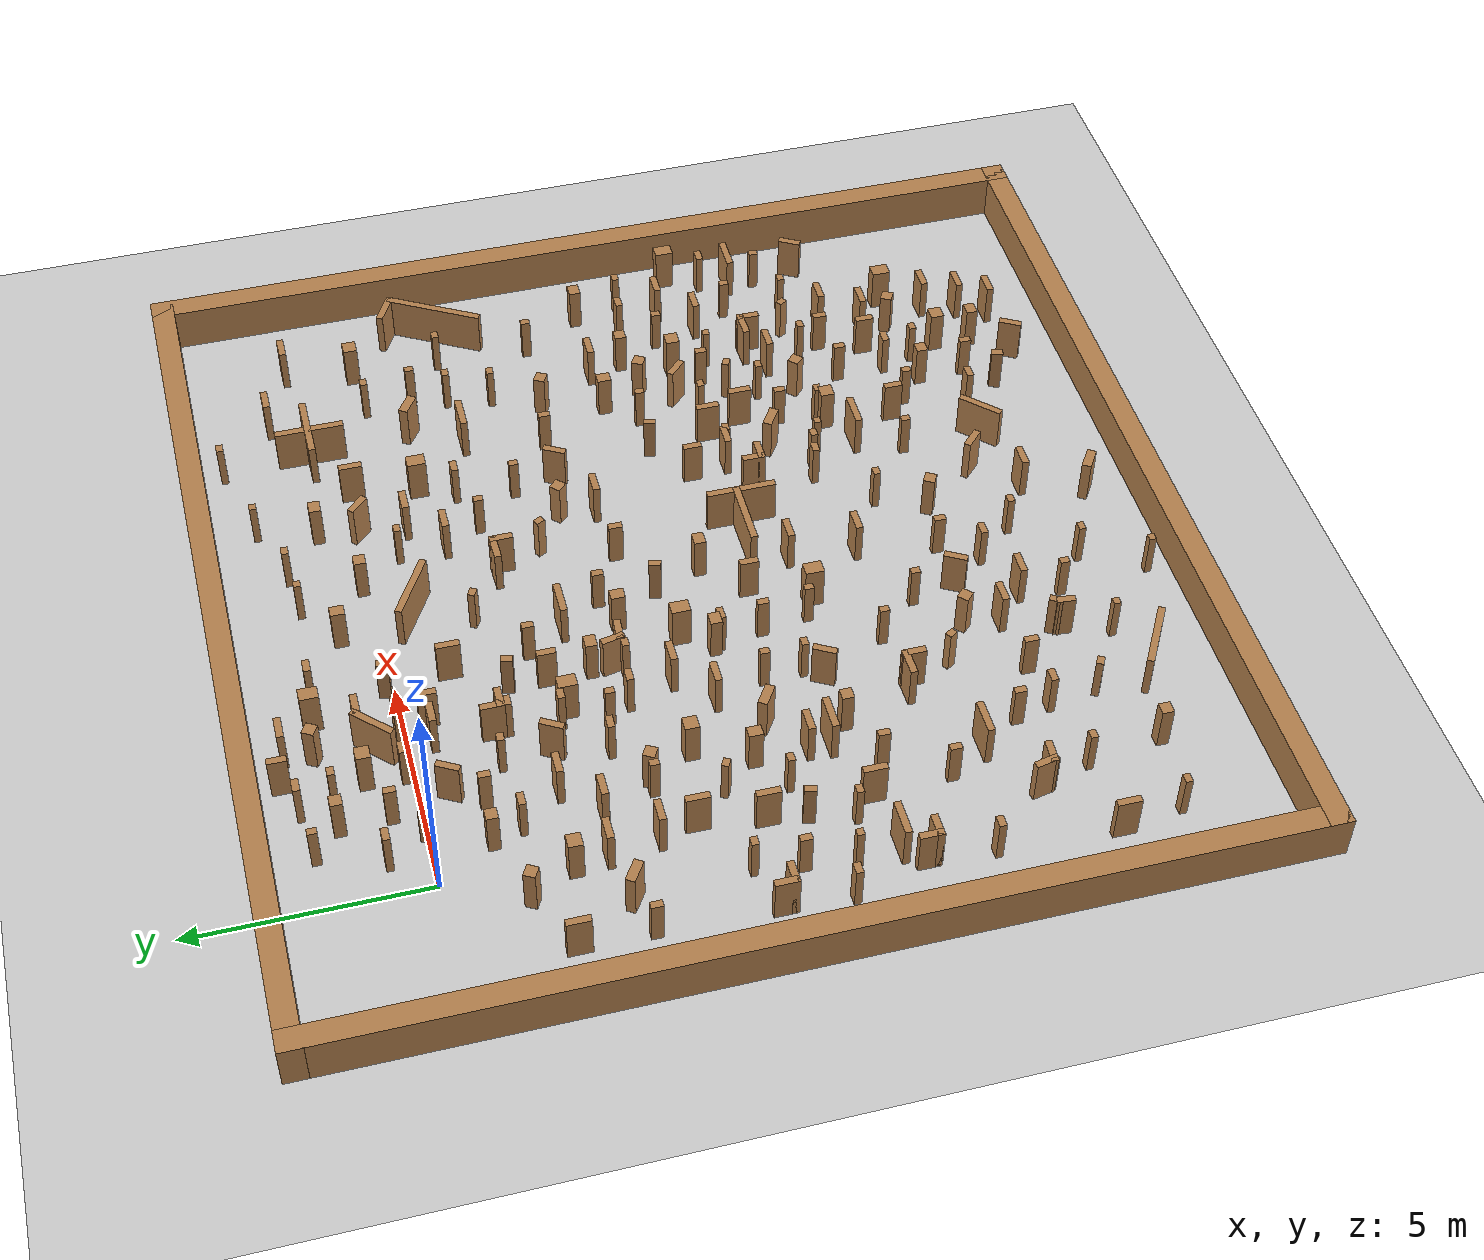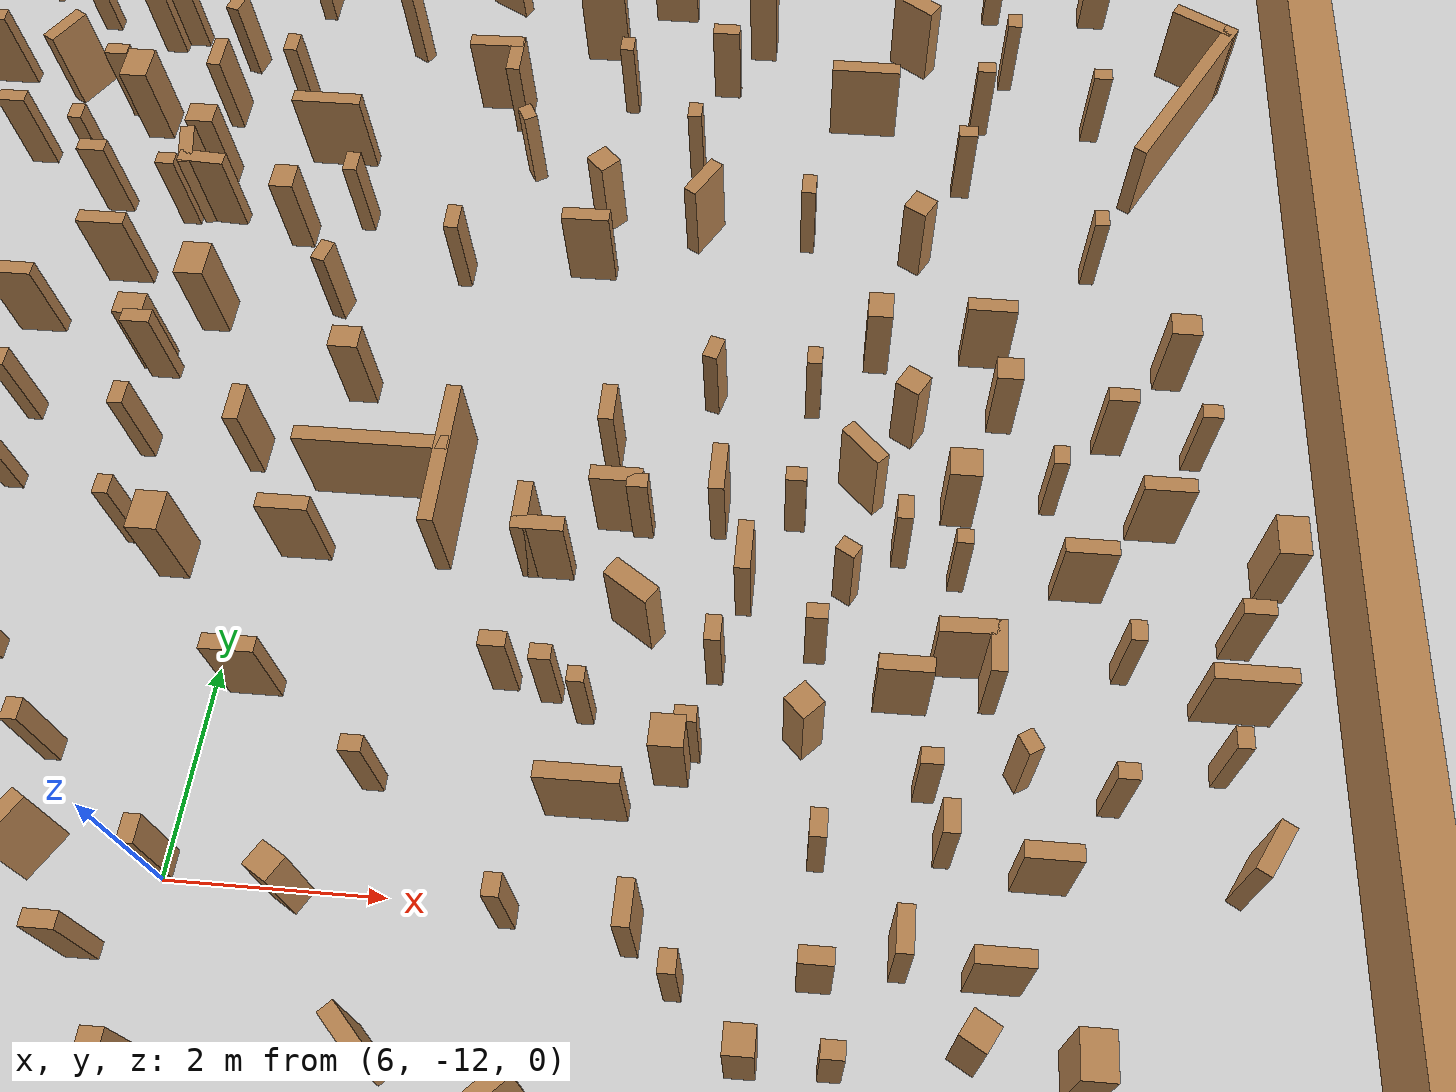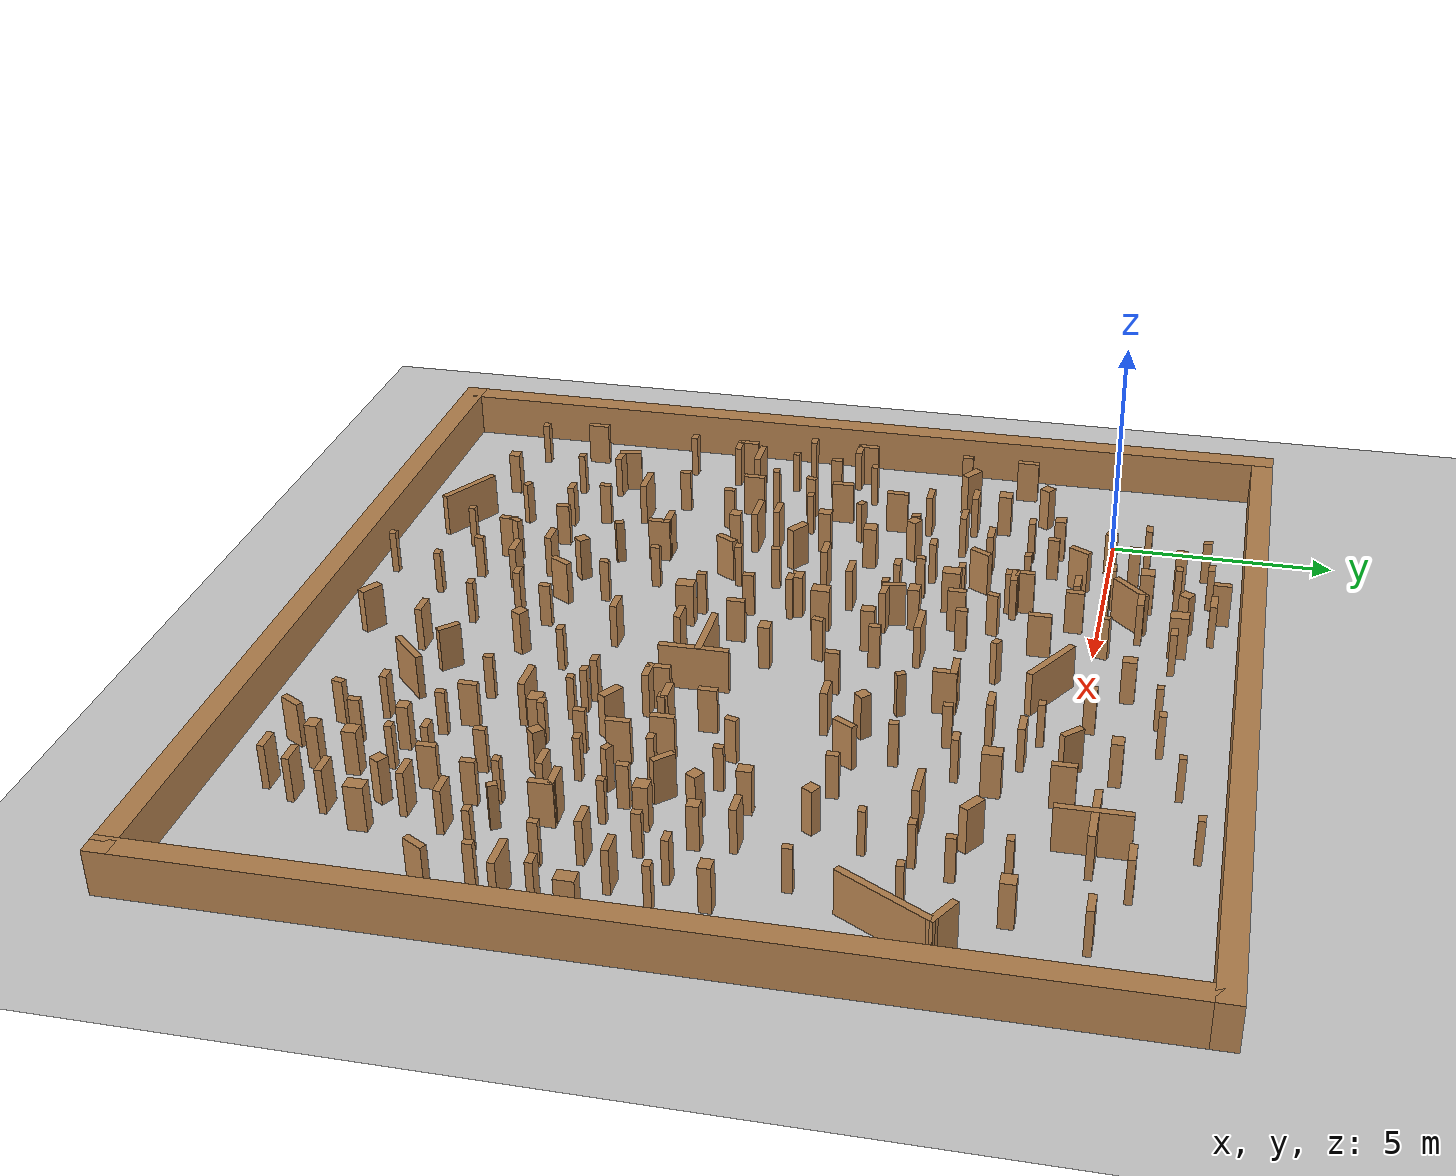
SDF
<sdf version="1.7">
 <world name="default">
  <light name="sun" type="directional">
   <pose>0 0 10 0 -0 0</pose>
   <diffuse>0.8 0.8 0.8 1</diffuse>
   <specular>0.2 0.2 0.2 1</specular>
   <attenuation>
    <range>1000</range>
    <constant>0.9</constant>
    <linear>0.01</linear>
    <quadratic>0.001</quadratic>
   </attenuation>
   <direction>-0.5 0.1 -0.9</direction>
   <spot><inner_angle>0</inner_angle><outer_angle>0</outer_angle><falloff>0</falloff></spot>
  </light>
  <model name="ground_plane">
   <static>1</static>
   <link name="link">
    <collision name="collision">
     <geometry><plane><normal>0 0 1</normal><size>100 100</size></plane></geometry>
     <surface><friction><ode><mu>100</mu><mu2>50</mu2></ode></friction></surface>
    </collision>
    <visual name="visual">
     <cast_shadows>0</cast_shadows>
     <geometry><plane><normal>0 0 1</normal><size>100 100</size></plane></geometry>
     <material>
      <script><uri>file://media/materials/scripts/gazebo.material</uri><name>Gazebo/Grey</name></script>
     </material>
    </visual>
   </link>
  </model>
  <gravity>0 0 -9.8</gravity>
  <magnetic_field>6e-06 2.3e-05 -4.2e-05</magnetic_field>
  <atmosphere type="adiabatic"/>
  <physics type="ode">
   <max_step_size>0.001</max_step_size>
   <real_time_factor>1</real_time_factor>
   <real_time_update_rate>1000</real_time_update_rate>
  </physics>
  <scene><ambient>0.4 0.4 0.4 1</ambient><background>0.7 0.7 0.7 1</background><shadows>1</shadows></scene>
  <spherical_coordinates>
   <surface_model>EARTH_WGS84</surface_model>
   <latitude_deg>0</latitude_deg>
   <longitude_deg>0</longitude_deg>
   <elevation>0</elevation>
   <heading_deg>0</heading_deg>
  </spherical_coordinates>
  <model name="boundary20x20">
   <pose>6.69964 -6.73932 0 0 -0 0</pose>
   <link name="Wall_0">
    <collision name="Wall_0_Collision">
     <geometry><box><size>20.5 0.5 1</size></box></geometry>
     <pose>0 0 0.5 0 -0 0</pose>
    </collision>
    <visual name="Wall_0_Visual">
     <pose>0 0 0.5 0 -0 0</pose>
     <geometry><box><size>20.5 0.5 1</size></box></geometry>
     <material>
      <script><uri>file://media/materials/scripts/gazebo.material</uri><name>Gazebo/Wood</name></script>
      <ambient>1 1 1 1</ambient>
     </material>
     <meta><layer>0</layer></meta>
    </visual>
    <pose>0 -10 0 0 -0 0</pose>
   </link>
   <link name="Wall_2">
    <collision name="Wall_2_Collision">
     <geometry><box><size>20.5 0.5 1</size></box></geometry>
     <pose>0 0 0.5 0 -0 0</pose>
    </collision>
    <visual name="Wall_2_Visual">
     <pose>0 0 0.5 0 -0 0</pose>
     <geometry><box><size>20.5 0.5 1</size></box></geometry>
     <material>
      <script><uri>file://media/materials/scripts/gazebo.material</uri><name>Gazebo/Wood</name></script>
      <ambient>1 1 1 1</ambient>
     </material>
     <meta><layer>0</layer></meta>
    </visual>
    <pose>-10 0 0 0 -0 -1.5708</pose>
   </link>
   <link name="Wall_4">
    <collision name="Wall_4_Collision">
     <geometry><box><size>20.5 0.5 1</size></box></geometry>
     <pose>0 0 0.5 0 -0 0</pose>
    </collision>
    <visual name="Wall_4_Visual">
     <pose>0 0 0.5 0 -0 0</pose>
     <geometry><box><size>20.5 0.5 1</size></box></geometry>
     <material>
      <script><uri>file://media/materials/scripts/gazebo.material</uri><name>Gazebo/Wood</name></script>
      <ambient>1 1 1 1</ambient>
     </material>
     <meta><layer>0</layer></meta>
    </visual>
    <pose>0 10 0 0 -0 0</pose>
   </link>
   <link name="Wall_8">
    <collision name="Wall_8_Collision">
     <geometry><box><size>20.5 0.5 1</size></box></geometry>
     <pose>0 0 0.5 0 -0 0</pose>
    </collision>
    <visual name="Wall_8_Visual">
     <pose>0 0 0.5 0 -0 0</pose>
     <geometry><box><size>20.5 0.5 1</size></box></geometry>
     <material>
      <script><uri>file://media/materials/scripts/gazebo.material</uri><name>Gazebo/Wood</name></script>
      <ambient>1 1 1 1</ambient>
     </material>
     <meta><layer>0</layer></meta>
    </visual>
    <pose>10 0 0 0 -0 1.5708</pose>
   </link>
   <static>1</static>
  </model>
  <model name="t1">
   <pose>4.20156 -11.2326 0 0 -0 0</pose>
   <link name="Wall_0">
    <collision name="Wall_0_Collision">
     <geometry><box><size>0.5 0.15 1</size></box></geometry>
     <pose>0 0 0.5 0 -0 0</pose>
    </collision>
    <visual name="Wall_0_Visual">
     <pose>0 0 0.5 0 -0 0</pose>
     <geometry><box><size>0.5 0.15 1</size></box></geometry>
     <material>
      <script><uri>file://media/materials/scripts/gazebo.material</uri><name>Gazebo/Wood</name></script>
      <ambient>1 1 1 1</ambient>
     </material>
     <meta><layer>0</layer></meta>
    </visual>
    <pose>0.174862 -1.84619 0 0 -0 0</pose>
   </link>
   <link name="Wall_10">
    <collision name="Wall_10_Collision">
     <geometry><box><size>0.16 0.15 1</size></box></geometry>
     <pose>0 0 0.5 0 -0 0</pose>
    </collision>
    <visual name="Wall_10_Visual">
     <pose>0 0 0.5 0 -0 0</pose>
     <geometry><box><size>0.16 0.15 1</size></box></geometry>
     <material>
      <script><uri>file://media/materials/scripts/gazebo.material</uri><name>Gazebo/Wood</name></script>
      <ambient>1 1 1 1</ambient>
     </material>
     <meta><layer>0</layer></meta>
    </visual>
    <pose>-1.33848 -3.38558 0 0 -0 0</pose>
   </link>
   <link name="Wall_101">
    <collision name="Wall_101_Collision">
     <geometry><box><size>0.3 0.25 1</size></box></geometry>
     <pose>0 0 0.5 0 -0 0</pose>
    </collision>
    <visual name="Wall_101_Visual">
     <pose>0 0 0.5 0 -0 0</pose>
     <geometry><box><size>0.3 0.25 1</size></box></geometry>
     <material>
      <script><uri>file://media/materials/scripts/gazebo.material</uri><name>Gazebo/Wood</name></script>
      <ambient>1 1 1 1</ambient>
     </material>
     <meta><layer>0</layer></meta>
    </visual>
    <pose>0.24444 4.67323 0 0 -0 0</pose>
   </link>
   <link name="Wall_103">
    <collision name="Wall_103_Collision">
     <geometry><box><size>0.3 0.25 1</size></box></geometry>
     <pose>0 0 0.5 0 -0 0</pose>
    </collision>
    <visual name="Wall_103_Visual">
     <pose>0 0 0.5 0 -0 0</pose>
     <geometry><box><size>0.3 0.25 1</size></box></geometry>
     <material>
      <script><uri>file://media/materials/scripts/gazebo.material</uri><name>Gazebo/Wood</name></script>
      <ambient>1 1 1 1</ambient>
     </material>
     <meta><layer>0</layer></meta>
    </visual>
    <pose>-2.80345 4.66938 0 0 -0 -1.5708</pose>
   </link>
   <link name="Wall_105">
    <collision name="Wall_105_Collision">
     <geometry><box><size>0.4 0.15 1</size></box></geometry>
     <pose>0 0 0.5 0 -0 0</pose>
    </collision>
    <visual name="Wall_105_Visual">
     <pose>0 0 0.5 0 -0 0</pose>
     <geometry><box><size>0.4 0.15 1</size></box></geometry>
     <material>
      <script><uri>file://media/materials/scripts/gazebo.material</uri><name>Gazebo/Wood</name></script>
      <ambient>1 1 1 1</ambient>
     </material>
     <meta><layer>0</layer></meta>
    </visual>
    <pose>5.96232 -0.895745 0 0 -0 -1.5708</pose>
   </link>
   <link name="Wall_12">
    <collision name="Wall_12_Collision">
     <geometry><box><size>0.2 0.15 1</size></box></geometry>
     <pose>0 0 0.5 0 -0 0</pose>
    </collision>
    <visual name="Wall_12_Visual">
     <pose>0 0 0.5 0 -0 0</pose>
     <geometry><box><size>0.2 0.15 1</size></box></geometry>
     <material>
      <script><uri>file://media/materials/scripts/gazebo.material</uri><name>Gazebo/Wood</name></script>
      <ambient>1 1 1 1</ambient>
     </material>
     <meta><layer>0</layer></meta>
    </visual>
    <pose>-1.33098 0.15162 0 0 -0 -1.0472</pose>
   </link>
   <link name="Wall_14">
    <collision name="Wall_14_Collision">
     <geometry><box><size>0.3 0.15 1</size></box></geometry>
     <pose>0 0 0.5 0 -0 0</pose>
    </collision>
    <visual name="Wall_14_Visual">
     <pose>0 0 0.5 0 -0 0</pose>
     <geometry><box><size>0.3 0.15 1</size></box></geometry>
     <material>
      <script><uri>file://media/materials/scripts/gazebo.material</uri><name>Gazebo/Wood</name></script>
      <ambient>1 1 1 1</ambient>
     </material>
     <meta><layer>0</layer></meta>
    </visual>
    <pose>-1.87614 -1.36219 0 0 -0 -1.5708</pose>
   </link>
   <link name="Wall_16">
    <collision name="Wall_16_Collision">
     <geometry><box><size>0.5 0.15 1</size></box></geometry>
     <pose>0 0 0.5 0 -0 0</pose>
    </collision>
    <visual name="Wall_16_Visual">
     <pose>0 0 0.5 0 -0 0</pose>
     <geometry><box><size>0.5 0.15 1</size></box></geometry>
     <material>
      <script><uri>file://media/materials/scripts/gazebo.material</uri><name>Gazebo/Wood</name></script>
      <ambient>1 1 1 1</ambient>
     </material>
     <meta><layer>0</layer></meta>
    </visual>
    <pose>3.92086 -2.06469 0 0 -0 -0.783378</pose>
   </link>
   <link name="Wall_18">
    <collision name="Wall_18_Collision">
     <geometry><box><size>0.2 0.15 1</size></box></geometry>
     <pose>0 0 0.5 0 -0 0</pose>
    </collision>
    <visual name="Wall_18_Visual">
     <pose>0 0 0.5 0 -0 0</pose>
     <geometry><box><size>0.2 0.15 1</size></box></geometry>
     <material>
      <script><uri>file://media/materials/scripts/gazebo.material</uri><name>Gazebo/Wood</name></script>
      <ambient>1 1 1 1</ambient>
     </material>
     <meta><layer>0</layer></meta>
    </visual>
    <pose>0.847759 -3.42904 0 0 -0 0</pose>
   </link>
   <link name="Wall_2">
    <collision name="Wall_2_Collision">
     <geometry><box><size>0.2 0.15 1</size></box></geometry>
     <pose>0 0 0.5 0 -0 0</pose>
    </collision>
    <visual name="Wall_2_Visual">
     <pose>0 0 0.5 0 -0 0</pose>
     <geometry><box><size>0.2 0.15 1</size></box></geometry>
     <material>
      <script><uri>file://media/materials/scripts/gazebo.material</uri><name>Gazebo/Wood</name></script>
      <ambient>1 1 1 1</ambient>
     </material>
     <meta><layer>0</layer></meta>
    </visual>
    <pose>1.98486 -2.25619 0 0 -0 3.14159</pose>
   </link>
   <link name="Wall_21">
    <collision name="Wall_21_Collision">
     <geometry><box><size>0.500017 0.2 1</size></box></geometry>
     <pose>0 0 0.5 0 -0 0</pose>
    </collision>
    <visual name="Wall_21_Visual">
     <pose>0 0 0.5 0 -0 0</pose>
     <geometry><box><size>0.500017 0.2 1</size></box></geometry>
     <material>
      <script><uri>file://media/materials/scripts/gazebo.material</uri><name>Gazebo/Wood</name></script>
      <ambient>1 1 1 1</ambient>
     </material>
     <meta><layer>0</layer></meta>
    </visual>
    <pose>2.69564 -4.29723 0 0 -0 -0.586607</pose>
   </link>
   <link name="Wall_23">
    <collision name="Wall_23_Collision">
     <geometry><box><size>0.16 0.15 1</size></box></geometry>
     <pose>0 0 0.5 0 -0 0</pose>
    </collision>
    <visual name="Wall_23_Visual">
     <pose>0 0 0.5 0 -0 0</pose>
     <geometry><box><size>0.16 0.15 1</size></box></geometry>
     <material>
      <script><uri>file://media/materials/scripts/gazebo.material</uri><name>Gazebo/Wood</name></script>
      <ambient>1 1 1 1</ambient>
     </material>
     <meta><layer>0</layer></meta>
    </visual>
    <pose>0.173217 -4.74438 0 0 -0 0</pose>
   </link>
   <link name="Wall_25">
    <collision name="Wall_25_Collision">
     <geometry><box><size>0.2 0.15 1</size></box></geometry>
     <pose>0 0 0.5 0 -0 0</pose>
    </collision>
    <visual name="Wall_25_Visual">
     <pose>0 0 0.5 0 -0 0</pose>
     <geometry><box><size>0.2 0.15 1</size></box></geometry>
     <material>
      <script><uri>file://media/materials/scripts/gazebo.material</uri><name>Gazebo/Wood</name></script>
      <ambient>1 1 1 1</ambient>
     </material>
     <meta><layer>0</layer></meta>
    </visual>
    <pose>0.492317 0.334728 0 0 -0 -1.5708</pose>
   </link>
   <link name="Wall_27">
    <collision name="Wall_27_Collision">
     <geometry><box><size>0.2 0.15 1</size></box></geometry>
     <pose>0 0 0.5 0 -0 0</pose>
    </collision>
    <visual name="Wall_27_Visual">
     <pose>0 0 0.5 0 -0 0</pose>
     <geometry><box><size>0.2 0.15 1</size></box></geometry>
     <material>
      <script><uri>file://media/materials/scripts/gazebo.material</uri><name>Gazebo/Wood</name></script>
      <ambient>1 1 1 1</ambient>
     </material>
     <meta><layer>0</layer></meta>
    </visual>
    <pose>3.47401 0.25916 0 0 -0 0</pose>
   </link>
   <link name="Wall_29">
    <collision name="Wall_29_Collision">
     <geometry><box><size>0.2 0.15 1</size></box></geometry>
     <pose>0 0 0.5 0 -0 0</pose>
    </collision>
    <visual name="Wall_29_Visual">
     <pose>0 0 0.5 0 -0 0</pose>
     <geometry><box><size>0.2 0.15 1</size></box></geometry>
     <material>
      <script><uri>file://media/materials/scripts/gazebo.material</uri><name>Gazebo/Wood</name></script>
      <ambient>1 1 1 1</ambient>
     </material>
     <meta><layer>0</layer></meta>
    </visual>
    <pose>-2.76454 -2.5089 0 0 -0 -0.523599</pose>
   </link>
   <link name="Wall_31">
    <collision name="Wall_31_Collision">
     <geometry><box><size>0.508166 0.15 1</size></box></geometry>
     <pose>0 0 0.5 0 -0 0</pose>
    </collision>
    <visual name="Wall_31_Visual">
     <pose>0 0 0.5 0 -0 0</pose>
     <geometry><box><size>0.508166 0.15 1</size></box></geometry>
     <material>
      <script><uri>file://media/materials/scripts/gazebo.material</uri><name>Gazebo/Wood</name></script>
      <ambient>1 1 1 1</ambient>
     </material>
     <meta><layer>0</layer></meta>
    </visual>
    <pose>-4.92012 -0.60019 0 0 -0 -1.35685</pose>
   </link>
   <link name="Wall_32">
    <collision name="Wall_32_Collision">
     <geometry><box><size>0.500227 0.15 1</size></box></geometry>
     <pose>0 0 0.5 0 -0 0</pose>
    </collision>
    <visual name="Wall_32_Visual">
     <pose>0 0 0.5 0 -0 0</pose>
     <geometry><box><size>0.500227 0.15 1</size></box></geometry>
     <material>
      <script><uri>file://media/materials/scripts/gazebo.material</uri><name>Gazebo/Wood</name></script>
      <ambient>1 1 1 1</ambient>
     </material>
     <meta><layer>0</layer></meta>
    </visual>
    <pose>-4.70726 -0.769794 0 0 -0 -0.056063</pose>
   </link>
   <link name="Wall_34">
    <collision name="Wall_34_Collision">
     <geometry><box><size>0.26 0.25 1</size></box></geometry>
     <pose>0 0 0.5 0 -0 0</pose>
    </collision>
    <visual name="Wall_34_Visual">
     <pose>0 0 0.5 0 -0 0</pose>
     <geometry><box><size>0.26 0.25 1</size></box></geometry>
     <material>
      <script><uri>file://media/materials/scripts/gazebo.material</uri><name>Gazebo/Wood</name></script>
      <ambient>1 1 1 1</ambient>
     </material>
     <meta><layer>0</layer></meta>
    </visual>
    <pose>-0.411989 -0.452656 0 0 -0 -0.785398</pose>
   </link>
   <link name="Wall_36">
    <collision name="Wall_36_Collision">
     <geometry><box><size>0.26 0.25 1</size></box></geometry>
     <pose>0 0 0.5 0 -0 0</pose>
    </collision>
    <visual name="Wall_36_Visual">
     <pose>0 0 0.5 0 -0 0</pose>
     <geometry><box><size>0.26 0.25 1</size></box></geometry>
     <material>
      <script><uri>file://media/materials/scripts/gazebo.material</uri><name>Gazebo/Wood</name></script>
      <ambient>1 1 1 1</ambient>
     </material>
     <meta><layer>0</layer></meta>
    </visual>
    <pose>-4.25021 -3.31732 0 0 -0 0</pose>
   </link>
   <link name="Wall_38">
    <collision name="Wall_38_Collision">
     <geometry><box><size>0.26 0.25 1</size></box></geometry>
     <pose>0 0 0.5 0 -0 0</pose>
    </collision>
    <visual name="Wall_38_Visual">
     <pose>0 0 0.5 0 -0 0</pose>
     <geometry><box><size>0.26 0.25 1</size></box></geometry>
     <material>
      <script><uri>file://media/materials/scripts/gazebo.material</uri><name>Gazebo/Wood</name></script>
      <ambient>1 1 1 1</ambient>
     </material>
     <meta><layer>0</layer></meta>
    </visual>
    <pose>2.98901 -0.79858 0 0 -0 -0.523599</pose>
   </link>
   <link name="Wall_4">
    <collision name="Wall_4_Collision">
     <geometry><box><size>0.2 0.15 1</size></box></geometry>
     <pose>0 0 0.5 0 -0 0</pose>
    </collision>
    <visual name="Wall_4_Visual">
     <pose>0 0 0.5 0 -0 0</pose>
     <geometry><box><size>0.2 0.15 1</size></box></geometry>
     <material>
      <script><uri>file://media/materials/scripts/gazebo.material</uri><name>Gazebo/Wood</name></script>
      <ambient>1 1 1 1</ambient>
     </material>
     <meta><layer>0</layer></meta>
    </visual>
    <pose>4.8769 -0.840298 0 0 -0 -1.5708</pose>
   </link>
   <link name="Wall_40">
    <collision name="Wall_40_Collision">
     <geometry><box><size>0.290798 0.15 1</size></box></geometry>
     <pose>0 0 0.5 0 -0 0</pose>
    </collision>
    <visual name="Wall_40_Visual">
     <pose>0 0 0.5 0 -0 0</pose>
     <geometry><box><size>0.290798 0.15 1</size></box></geometry>
     <material>
      <script><uri>file://media/materials/scripts/gazebo.material</uri><name>Gazebo/Wood</name></script>
      <ambient>1 1 1 1</ambient>
     </material>
     <meta><layer>0</layer></meta>
    </visual>
    <pose>-0.984833 -2.22049 0 0 -0 -2.12928</pose>
   </link>
   <link name="Wall_41">
    <collision name="Wall_41_Collision">
     <geometry><box><size>0.396924 0.15 1</size></box></geometry>
     <pose>0 0 0.5 0 -0 0</pose>
    </collision>
    <visual name="Wall_41_Visual">
     <pose>0 0 0.5 0 -0 0</pose>
     <geometry><box><size>0.396924 0.15 1</size></box></geometry>
     <material>
      <script><uri>file://media/materials/scripts/gazebo.material</uri><name>Gazebo/Wood</name></script>
      <ambient>1 1 1 1</ambient>
     </material>
     <meta><layer>0</layer></meta>
    </visual>
    <pose>-1.03314 -2.40319 0 0 -0 -1.65999</pose>
   </link>
   <link name="Wall_43">
    <collision name="Wall_43_Collision">
     <geometry><box><size>1 0.15 1</size></box></geometry>
     <pose>0 0 0.5 0 -0 0</pose>
    </collision>
    <visual name="Wall_43_Visual">
     <pose>0 0 0.5 0 -0 0</pose>
     <geometry><box><size>1 0.15 1</size></box></geometry>
     <material>
      <script><uri>file://media/materials/scripts/gazebo.material</uri><name>Gazebo/Wood</name></script>
      <ambient>1 1 1 1</ambient>
     </material>
     <meta><layer>0</layer></meta>
    </visual>
    <pose>4.87736 -2.57969 0 0 -0 -2.35619</pose>
   </link>
   <link name="Wall_45">
    <collision name="Wall_45_Collision">
     <geometry><box><size>1.5 0.15 1</size></box></geometry>
     <pose>0 0 0.5 0 -0 0</pose>
    </collision>
    <visual name="Wall_45_Visual">
     <pose>0 0 0.5 0 -0 0</pose>
     <geometry><box><size>1.5 0.15 1</size></box></geometry>
     <material>
      <script><uri>file://media/materials/scripts/gazebo.material</uri><name>Gazebo/Wood</name></script>
      <ambient>1 1 1 1</ambient>
     </material>
     <meta><layer>0</layer></meta>
    </visual>
    <pose>-2.38364 -3.84369 0 0 -0 -0.523649</pose>
   </link>
   <link name="Wall_47">
    <collision name="Wall_47_Collision">
     <geometry><box><size>0.5 0.15 1</size></box></geometry>
     <pose>0 0 0.5 0 -0 0</pose>
    </collision>
    <visual name="Wall_47_Visual">
     <pose>0 0 0.5 0 -0 0</pose>
     <geometry><box><size>0.5 0.15 1</size></box></geometry>
     <material>
      <script><uri>file://media/materials/scripts/gazebo.material</uri><name>Gazebo/Wood</name></script>
      <ambient>1 1 1 1</ambient>
     </material>
     <meta><layer>0</layer></meta>
    </visual>
    <pose>-6.22714 -1.79019 0 0 -0 -1.5708</pose>
   </link>
   <link name="Wall_49">
    <collision name="Wall_49_Collision">
     <geometry><box><size>0.2 0.15 1</size></box></geometry>
     <pose>0 0 0.5 0 -0 0</pose>
    </collision>
    <visual name="Wall_49_Visual">
     <pose>0 0 0.5 0 -0 0</pose>
     <geometry><box><size>0.2 0.15 1</size></box></geometry>
     <material>
      <script><uri>file://media/materials/scripts/gazebo.material</uri><name>Gazebo/Wood</name></script>
      <ambient>1 1 1 1</ambient>
     </material>
     <meta><layer>0</layer></meta>
    </visual>
    <pose>-4.51214 -1.69619 0 0 -0 0</pose>
   </link>
   <link name="Wall_51">
    <collision name="Wall_51_Collision">
     <geometry><box><size>0.598262 0.15 1</size></box></geometry>
     <pose>0 0 0.5 0 -0 0</pose>
    </collision>
    <visual name="Wall_51_Visual">
     <pose>0 0 0.5 0 -0 0</pose>
     <geometry><box><size>0.598262 0.15 1</size></box></geometry>
     <material>
      <script><uri>file://media/materials/scripts/gazebo.material</uri><name>Gazebo/Wood</name></script>
      <ambient>1 1 1 1</ambient>
     </material>
     <meta><layer>0</layer></meta>
    </visual>
    <pose>-1.84166 1.19866 0 0 -0 0.021322</pose>
   </link>
   <link name="Wall_52">
    <collision name="Wall_52_Collision">
     <geometry><box><size>0.5 0.15 1</size></box></geometry>
     <pose>0 0 0.5 0 -0 0</pose>
    </collision>
    <visual name="Wall_52_Visual">
     <pose>0 0 0.5 0 -0 0</pose>
     <geometry><box><size>0.5 0.15 1</size></box></geometry>
     <material>
      <script><uri>file://media/materials/scripts/gazebo.material</uri><name>Gazebo/Wood</name></script>
      <ambient>1 1 1 1</ambient>
     </material>
     <meta><layer>0</layer></meta>
    </visual>
    <pose>-1.60237 1.02843 0 0 -0 -1.5708</pose>
   </link>
   <link name="Wall_54">
    <collision name="Wall_54_Collision">
     <geometry><box><size>0.5 0.15 1</size></box></geometry>
     <pose>0 0 0.5 0 -0 0</pose>
    </collision>
    <visual name="Wall_54_Visual">
     <pose>0 0 0.5 0 -0 0</pose>
     <geometry><box><size>0.5 0.15 1</size></box></geometry>
     <material>
      <script><uri>file://media/materials/scripts/gazebo.material</uri><name>Gazebo/Wood</name></script>
      <ambient>1 1 1 1</ambient>
     </material>
     <meta><layer>0</layer></meta>
    </visual>
    <pose>2.18786 1.08981 0 0 -0 0</pose>
   </link>
   <link name="Wall_56">
    <collision name="Wall_56_Collision">
     <geometry><box><size>0.25 0.15 1</size></box></geometry>
     <pose>0 0 0.5 0 -0 0</pose>
    </collision>
    <visual name="Wall_56_Visual">
     <pose>0 0 0.5 0 -0 0</pose>
     <geometry><box><size>0.25 0.15 1</size></box></geometry>
     <material>
      <script><uri>file://media/materials/scripts/gazebo.material</uri><name>Gazebo/Wood</name></script>
      <ambient>1 1 1 1</ambient>
     </material>
     <meta><layer>0</layer></meta>
    </visual>
    <pose>-4.14014 0.99381 0 0 -0 -1.5708</pose>
   </link>
   <link name="Wall_58">
    <collision name="Wall_58_Collision">
     <geometry><box><size>0.5 0.15 1</size></box></geometry>
     <pose>0 0 0.5 0 -0 0</pose>
    </collision>
    <visual name="Wall_58_Visual">
     <pose>0 0 0.5 0 -0 0</pose>
     <geometry><box><size>0.5 0.15 1</size></box></geometry>
     <material>
      <script><uri>file://media/materials/scripts/gazebo.material</uri><name>Gazebo/Wood</name></script>
      <ambient>1 1 1 1</ambient>
     </material>
     <meta><layer>0</layer></meta>
    </visual>
    <pose>3.15886 -2.93519 0 0 -0 0</pose>
   </link>
   <link name="Wall_6">
    <collision name="Wall_6_Collision">
     <geometry><box><size>0.25 0.15 1</size></box></geometry>
     <pose>0 0 0.5 0 -0 0</pose>
    </collision>
    <visual name="Wall_6_Visual">
     <pose>0 0 0.5 0 -0 0</pose>
     <geometry><box><size>0.25 0.15 1</size></box></geometry>
     <material>
      <script><uri>file://media/materials/scripts/gazebo.material</uri><name>Gazebo/Wood</name></script>
      <ambient>1 1 1 1</ambient>
     </material>
     <meta><layer>0</layer></meta>
    </visual>
    <pose>1.80473 -0.621958 0 0 -0 -1.5708</pose>
   </link>
   <link name="Wall_60">
    <collision name="Wall_60_Collision">
     <geometry><box><size>0.3 0.15 1</size></box></geometry>
     <pose>0 0 0.5 0 -0 0</pose>
    </collision>
    <visual name="Wall_60_Visual">
     <pose>0 0 0.5 0 -0 0</pose>
     <geometry><box><size>0.3 0.15 1</size></box></geometry>
     <material>
      <script><uri>file://media/materials/scripts/gazebo.material</uri><name>Gazebo/Wood</name></script>
      <ambient>1 1 1 1</ambient>
     </material>
     <meta><layer>0</layer></meta>
    </visual>
    <pose>1.30104 -1.40827 0 0 -0 0</pose>
   </link>
   <link name="Wall_62">
    <collision name="Wall_62_Collision">
     <geometry><box><size>0.2 0.15 1</size></box></geometry>
     <pose>0 0 0.5 0 -0 0</pose>
    </collision>
    <visual name="Wall_62_Visual">
     <pose>0 0 0.5 0 -0 0</pose>
     <geometry><box><size>0.2 0.15 1</size></box></geometry>
     <material>
      <script><uri>file://media/materials/scripts/gazebo.material</uri><name>Gazebo/Wood</name></script>
      <ambient>1 1 1 1</ambient>
     </material>
     <meta><layer>0</layer></meta>
    </visual>
    <pose>-0.369971 1.27302 0 0 -0 -1.5708</pose>
   </link>
   <link name="Wall_64">
    <collision name="Wall_64_Collision">
     <geometry><box><size>0.5 0.15 1</size></box></geometry>
     <pose>0 0 0.5 0 -0 0</pose>
    </collision>
    <visual name="Wall_64_Visual">
     <pose>0 0 0.5 0 -0 0</pose>
     <geometry><box><size>0.5 0.15 1</size></box></geometry>
     <material>
      <script><uri>file://media/materials/scripts/gazebo.material</uri><name>Gazebo/Wood</name></script>
      <ambient>1 1 1 1</ambient>
     </material>
     <meta><layer>0</layer></meta>
    </visual>
    <pose>0.676362 -0.61169 0 0 -0 -2.09455</pose>
   </link>
   <link name="Wall_66">
    <collision name="Wall_66_Collision">
     <geometry><box><size>0.2 0.15 1</size></box></geometry>
     <pose>0 0 0.5 0 -0 0</pose>
    </collision>
    <visual name="Wall_66_Visual">
     <pose>0 0 0.5 0 -0 0</pose>
     <geometry><box><size>0.2 0.15 1</size></box></geometry>
     <material>
      <script><uri>file://media/materials/scripts/gazebo.material</uri><name>Gazebo/Wood</name></script>
      <ambient>1 1 1 1</ambient>
     </material>
     <meta><layer>0</layer></meta>
    </visual>
    <pose>0.000119 -2.75171 0 0 -0 -1.5708</pose>
   </link>
   <link name="Wall_68">
    <collision name="Wall_68_Collision">
     <geometry><box><size>0.75 0.15 1</size></box></geometry>
     <pose>0 0 0.5 0 -0 0</pose>
    </collision>
    <visual name="Wall_68_Visual">
     <pose>0 0 0.5 0 -0 0</pose>
     <geometry><box><size>0.75 0.15 1</size></box></geometry>
     <material>
      <script><uri>file://media/materials/scripts/gazebo.material</uri><name>Gazebo/Wood</name></script>
      <ambient>1 1 1 1</ambient>
     </material>
     <meta><layer>0</layer></meta>
    </visual>
    <pose>-3.56314 0.18781 0 0 -0 0</pose>
   </link>
   <link name="Wall_70">
    <collision name="Wall_70_Collision">
     <geometry><box><size>0.3 0.15 1</size></box></geometry>
     <pose>0 0 0.5 0 -0 0</pose>
    </collision>
    <visual name="Wall_70_Visual">
     <pose>0 0 0.5 0 -0 0</pose>
     <geometry><box><size>0.3 0.15 1</size></box></geometry>
     <material>
      <script><uri>file://media/materials/scripts/gazebo.material</uri><name>Gazebo/Wood</name></script>
      <ambient>1 1 1 1</ambient>
     </material>
     <meta><layer>0</layer></meta>
    </visual>
    <pose>-2.8856 -1.45453 0 0 -0 0</pose>
   </link>
   <link name="Wall_72">
    <collision name="Wall_72_Collision">
     <geometry><box><size>0.2 0.15 1</size></box></geometry>
     <pose>0 0 0.5 0 -0 0</pose>
    </collision>
    <visual name="Wall_72_Visual">
     <pose>0 0 0.5 0 -0 0</pose>
     <geometry><box><size>0.2 0.15 1</size></box></geometry>
     <material>
      <script><uri>file://media/materials/scripts/gazebo.material</uri><name>Gazebo/Wood</name></script>
      <ambient>1 1 1 1</ambient>
     </material>
     <meta><layer>0</layer></meta>
    </visual>
    <pose>4.95194 1.22862 0 0 -0 0</pose>
   </link>
   <link name="Wall_74">
    <collision name="Wall_74_Collision">
     <geometry><box><size>0.2 0.15 1</size></box></geometry>
     <pose>0 0 0.5 0 -0 0</pose>
    </collision>
    <visual name="Wall_74_Visual">
     <pose>0 0 0.5 0 -0 0</pose>
     <geometry><box><size>0.2 0.15 1</size></box></geometry>
     <material>
      <script><uri>file://media/materials/scripts/gazebo.material</uri><name>Gazebo/Wood</name></script>
      <ambient>1 1 1 1</ambient>
     </material>
     <meta><layer>0</layer></meta>
    </visual>
    <pose>-5.98884 -3.07367 0 0 -0 0</pose>
   </link>
   <link name="Wall_76">
    <collision name="Wall_76_Collision">
     <geometry><box><size>0.5 0.15 1</size></box></geometry>
     <pose>0 0 0.5 0 -0 0</pose>
    </collision>
    <visual name="Wall_76_Visual">
     <pose>0 0 0.5 0 -0 0</pose>
     <geometry><box><size>0.5 0.15 1</size></box></geometry>
     <material>
      <script><uri>file://media/materials/scripts/gazebo.material</uri><name>Gazebo/Wood</name></script>
      <ambient>1 1 1 1</ambient>
     </material>
     <meta><layer>0</layer></meta>
    </visual>
    <pose>-0.496138 -1.22319 0 0 -0 0</pose>
   </link>
   <link name="Wall_78">
    <collision name="Wall_78_Collision">
     <geometry><box><size>0.31 0.3 1</size></box></geometry>
     <pose>0 0 0.5 0 -0 0</pose>
    </collision>
    <visual name="Wall_78_Visual">
     <pose>0 0 0.5 0 -0 0</pose>
     <geometry><box><size>0.31 0.3 1</size></box></geometry>
     <material>
      <script><uri>file://media/materials/scripts/gazebo.material</uri><name>Gazebo/Wood</name></script>
      <ambient>1 1 1 1</ambient>
     </material>
     <meta><layer>0</layer></meta>
    </visual>
    <pose>6.14714 0.591618 0 0 -0 0</pose>
   </link>
   <link name="Wall_8">
    <collision name="Wall_8_Collision">
     <geometry><box><size>0.25 0.15 1</size></box></geometry>
     <pose>0 0 0.5 0 -0 0</pose>
    </collision>
    <visual name="Wall_8_Visual">
     <pose>0 0 0.5 0 -0 0</pose>
     <geometry><box><size>0.25 0.15 1</size></box></geometry>
     <material>
      <script><uri>file://media/materials/scripts/gazebo.material</uri><name>Gazebo/Wood</name></script>
      <ambient>1 1 1 1</ambient>
     </material>
     <meta><layer>0</layer></meta>
    </visual>
    <pose>-3.09214 -0.69819 0 0 -0 -1.5708</pose>
   </link>
   <link name="Wall_80">
    <collision name="Wall_80_Collision">
     <geometry><box><size>0.4 0.3 1</size></box></geometry>
     <pose>0 0 0.5 0 -0 0</pose>
    </collision>
    <visual name="Wall_80_Visual">
     <pose>0 0 0.5 0 -0 0</pose>
     <geometry><box><size>0.4 0.3 1</size></box></geometry>
     <material>
      <script><uri>file://media/materials/scripts/gazebo.material</uri><name>Gazebo/Wood</name></script>
      <ambient>1 1 1 1</ambient>
     </material>
     <meta><layer>0</layer></meta>
    </visual>
    <pose>1.08922 2.35187 0 0 -0 1.5708</pose>
   </link>
   <link name="Wall_82">
    <collision name="Wall_82_Collision">
     <geometry><box><size>1.5 0.15 1</size></box></geometry>
     <pose>0 0 0.5 0 -0 0</pose>
    </collision>
    <visual name="Wall_82_Visual">
     <pose>0 0 0.5 0 -0 0</pose>
     <geometry><box><size>1.5 0.15 1</size></box></geometry>
     <material>
      <script><uri>file://media/materials/scripts/gazebo.material</uri><name>Gazebo/Wood</name></script>
      <ambient>1 1 1 1</ambient>
     </material>
     <meta><layer>0</layer></meta>
    </visual>
    <pose>3.68286 3.19981 0 0 -0 -1.5708</pose>
   </link>
   <link name="Wall_84">
    <collision name="Wall_84_Collision">
     <geometry><box><size>1.5 0.15 1</size></box></geometry>
     <pose>0 0 0.5 0 -0 0</pose>
    </collision>
    <visual name="Wall_84_Visual">
     <pose>0 0 0.5 0 -0 0</pose>
     <geometry><box><size>1.5 0.15 1</size></box></geometry>
     <material>
      <script><uri>file://media/materials/scripts/gazebo.material</uri><name>Gazebo/Wood</name></script>
      <ambient>1 1 1 1</ambient>
     </material>
     <meta><layer>0</layer></meta>
    </visual>
    <pose>2.99013 3.29827 0 0 -0 0</pose>
   </link>
   <link name="Wall_86">
    <collision name="Wall_86_Collision">
     <geometry><box><size>0.75 0.15 1</size></box></geometry>
     <pose>0 0 0.5 0 -0 0</pose>
    </collision>
    <visual name="Wall_86_Visual">
     <pose>0 0 0.5 0 -0 0</pose>
     <geometry><box><size>0.75 0.15 1</size></box></geometry>
     <material>
      <script><uri>file://media/materials/scripts/gazebo.material</uri><name>Gazebo/Wood</name></script>
      <ambient>1 1 1 1</ambient>
     </material>
     <meta><layer>0</layer></meta>
    </visual>
    <pose>-2.70314 3.09481 0 0 -0 0</pose>
   </link>
   <link name="Wall_88">
    <collision name="Wall_88_Collision">
     <geometry><box><size>0.5 0.15 1</size></box></geometry>
     <pose>0 0 0.5 0 -0 0</pose>
    </collision>
    <visual name="Wall_88_Visual">
     <pose>0 0 0.5 0 -0 0</pose>
     <geometry><box><size>0.5 0.15 1</size></box></geometry>
     <material>
      <script><uri>file://media/materials/scripts/gazebo.material</uri><name>Gazebo/Wood</name></script>
      <ambient>1 1 1 1</ambient>
     </material>
     <meta><layer>0</layer></meta>
    </visual>
    <pose>-6.03614 2.09581 0 0 -0 -1.5708</pose>
   </link>
   <link name="Wall_89">
    <collision name="Wall_89_Collision">
     <geometry><box><size>0.5 0.15 1</size></box></geometry>
     <pose>0 0 0.5 0 -0 0</pose>
    </collision>
    <visual name="Wall_89_Visual">
     <pose>0 0 0.5 0 -0 0</pose>
     <geometry><box><size>0.5 0.15 1</size></box></geometry>
     <material>
      <script><uri>file://media/materials/scripts/gazebo.material</uri><name>Gazebo/Wood</name></script>
      <ambient>1 1 1 1</ambient>
     </material>
     <meta><layer>0</layer></meta>
    </visual>
    <pose>-5.86114 1.92081 0 0 -0 0</pose>
   </link>
   <link name="Wall_91">
    <collision name="Wall_91_Collision">
     <geometry><box><size>0.25 0.15 1</size></box></geometry>
     <pose>0 0 0.5 0 -0 0</pose>
    </collision>
    <visual name="Wall_91_Visual">
     <pose>0 0 0.5 0 -0 0</pose>
     <geometry><box><size>0.25 0.15 1</size></box></geometry>
     <material>
      <script><uri>file://media/materials/scripts/gazebo.material</uri><name>Gazebo/Wood</name></script>
      <ambient>1 1 1 1</ambient>
     </material>
     <meta><layer>0</layer></meta>
    </visual>
    <pose>-6.07714 0.73081 0 0 -0 0</pose>
   </link>
   <link name="Wall_93">
    <collision name="Wall_93_Collision">
     <geometry><box><size>0.2 0.15 1</size></box></geometry>
     <pose>0 0 0.5 0 -0 0</pose>
    </collision>
    <visual name="Wall_93_Visual">
     <pose>0 0 0.5 0 -0 0</pose>
     <geometry><box><size>0.2 0.15 1</size></box></geometry>
     <material>
      <script><uri>file://media/materials/scripts/gazebo.material</uri><name>Gazebo/Wood</name></script>
      <ambient>1 1 1 1</ambient>
     </material>
     <meta><layer>0</layer></meta>
    </visual>
    <pose>-0.805032 3.09018 0 0 -0 0</pose>
   </link>
   <link name="Wall_95">
    <collision name="Wall_95_Collision">
     <geometry><box><size>0.25 0.15 1</size></box></geometry>
     <pose>0 0 0.5 0 -0 0</pose>
    </collision>
    <visual name="Wall_95_Visual">
     <pose>0 0 0.5 0 -0 0</pose>
     <geometry><box><size>0.25 0.15 1</size></box></geometry>
     <material>
      <script><uri>file://media/materials/scripts/gazebo.material</uri><name>Gazebo/Wood</name></script>
      <ambient>1 1 1 1</ambient>
     </material>
     <meta><layer>0</layer></meta>
    </visual>
    <pose>-4.42814 4.01331 0 0 -0 -1.83268</pose>
   </link>
   <link name="Wall_97">
    <collision name="Wall_97_Collision">
     <geometry><box><size>0.5 0.15 1</size></box></geometry>
     <pose>0 0 0.5 0 -0 0</pose>
    </collision>
    <visual name="Wall_97_Visual">
     <pose>0 0 0.5 0 -0 0</pose>
     <geometry><box><size>0.5 0.15 1</size></box></geometry>
     <material>
      <script><uri>file://media/materials/scripts/gazebo.material</uri><name>Gazebo/Wood</name></script>
      <ambient>1 1 1 1</ambient>
     </material>
     <meta><layer>0</layer></meta>
    </visual>
    <pose>5.38186 3.08981 0 0 -0 0</pose>
   </link>
   <link name="Wall_99">
    <collision name="Wall_99_Collision">
     <geometry><box><size>0.5 0.15 1</size></box></geometry>
     <pose>0 0 0.5 0 -0 0</pose>
    </collision>
    <visual name="Wall_99_Visual">
     <pose>0 0 0.5 0 -0 0</pose>
     <geometry><box><size>0.5 0.15 1</size></box></geometry>
     <material>
      <script><uri>file://media/materials/scripts/gazebo.material</uri><name>Gazebo/Wood</name></script>
      <ambient>1 1 1 1</ambient>
     </material>
     <meta><layer>0</layer></meta>
    </visual>
    <pose>-4.25314 2.66081 0 0 -0 -1.5708</pose>
   </link>
   <static>1</static>
  </model>
  <model name="t2">
   <pose>9.477 -1.34585 0 0 -0 0</pose>
   <link name="Wall_0">
    <collision name="Wall_0_Collision">
     <geometry><box><size>0.5 0.15 1</size></box></geometry>
     <pose>0 0 0.5 0 -0 0</pose>
    </collision>
    <visual name="Wall_0_Visual">
     <pose>0 0 0.5 0 -0 0</pose>
     <geometry><box><size>0.5 0.15 1</size></box></geometry>
     <material>
      <script><uri>file://media/materials/scripts/gazebo.material</uri><name>Gazebo/Wood</name></script>
      <ambient>1 1 1 1</ambient>
     </material>
     <meta><layer>0</layer></meta>
    </visual>
    <pose>-0.130152 0.326907 0 0 -0 0</pose>
   </link>
   <link name="Wall_10">
    <collision name="Wall_10_Collision">
     <geometry><box><size>0.16 0.15 1</size></box></geometry>
     <pose>0 0 0.5 0 -0 0</pose>
    </collision>
    <visual name="Wall_10_Visual">
     <pose>0 0 0.5 0 -0 0</pose>
     <geometry><box><size>0.16 0.15 1</size></box></geometry>
     <material>
      <script><uri>file://media/materials/scripts/gazebo.material</uri><name>Gazebo/Wood</name></script>
      <ambient>1 1 1 1</ambient>
     </material>
     <meta><layer>0</layer></meta>
    </visual>
    <pose>0.439698 3.46018 0 0 -0 0</pose>
   </link>
   <link name="Wall_101">
    <collision name="Wall_101_Collision">
     <geometry><box><size>0.3 0.25 1</size></box></geometry>
     <pose>0 0 0.5 0 -0 0</pose>
    </collision>
    <visual name="Wall_101_Visual">
     <pose>0 0 0.5 0 -0 0</pose>
     <geometry><box><size>0.3 0.25 1</size></box></geometry>
     <material>
      <script><uri>file://media/materials/scripts/gazebo.material</uri><name>Gazebo/Wood</name></script>
      <ambient>1 1 1 1</ambient>
     </material>
     <meta><layer>0</layer></meta>
    </visual>
    <pose>0.122968 2.19661 0 0 -0 0</pose>
   </link>
   <link name="Wall_103">
    <collision name="Wall_103_Collision">
     <geometry><box><size>0.3 0.25 1</size></box></geometry>
     <pose>0 0 0.5 0 -0 0</pose>
    </collision>
    <visual name="Wall_103_Visual">
     <pose>0 0 0.5 0 -0 0</pose>
     <geometry><box><size>0.3 0.25 1</size></box></geometry>
     <material>
      <script><uri>file://media/materials/scripts/gazebo.material</uri><name>Gazebo/Wood</name></script>
      <ambient>1 1 1 1</ambient>
     </material>
     <meta><layer>0</layer></meta>
    </visual>
    <pose>-2.92493 2.19276 0 0 -0 -1.5708</pose>
   </link>
   <link name="Wall_105">
    <collision name="Wall_105_Collision">
     <geometry><box><size>0.4 0.15 1</size></box></geometry>
     <pose>0 0 0.5 0 -0 0</pose>
    </collision>
    <visual name="Wall_105_Visual">
     <pose>0 0 0.5 0 -0 0</pose>
     <geometry><box><size>0.4 0.15 1</size></box></geometry>
     <material>
      <script><uri>file://media/materials/scripts/gazebo.material</uri><name>Gazebo/Wood</name></script>
      <ambient>1 1 1 1</ambient>
     </material>
     <meta><layer>0</layer></meta>
    </visual>
    <pose>-5.50813 0.818499 0 0 -0 -1.5708</pose>
   </link>
   <link name="Wall_12">
    <collision name="Wall_12_Collision">
     <geometry><box><size>0.2 0.15 1</size></box></geometry>
     <pose>0 0 0.5 0 -0 0</pose>
    </collision>
    <visual name="Wall_12_Visual">
     <pose>0 0 0.5 0 -0 0</pose>
     <geometry><box><size>0.2 0.15 1</size></box></geometry>
     <material>
      <script><uri>file://media/materials/scripts/gazebo.material</uri><name>Gazebo/Wood</name></script>
      <ambient>1 1 1 1</ambient>
     </material>
     <meta><layer>0</layer></meta>
    </visual>
    <pose>-1.45246 -2.325 0 0 -0 -1.0472</pose>
   </link>
   <link name="Wall_14">
    <collision name="Wall_14_Collision">
     <geometry><box><size>0.3 0.15 1</size></box></geometry>
     <pose>0 0 0.5 0 -0 0</pose>
    </collision>
    <visual name="Wall_14_Visual">
     <pose>0 0 0.5 0 -0 0</pose>
     <geometry><box><size>0.3 0.15 1</size></box></geometry>
     <material>
      <script><uri>file://media/materials/scripts/gazebo.material</uri><name>Gazebo/Wood</name></script>
      <ambient>1 1 1 1</ambient>
     </material>
     <meta><layer>0</layer></meta>
    </visual>
    <pose>-1.99761 -3.83881 0 0 -0 -1.5708</pose>
   </link>
   <link name="Wall_16">
    <collision name="Wall_16_Collision">
     <geometry><box><size>0.500019 0.15 1</size></box></geometry>
     <pose>0 0 0.5 0 -0 0</pose>
    </collision>
    <visual name="Wall_16_Visual">
     <pose>0 0 0.5 0 -0 0</pose>
     <geometry><box><size>0.500019 0.15 1</size></box></geometry>
     <material>
      <script><uri>file://media/materials/scripts/gazebo.material</uri><name>Gazebo/Wood</name></script>
      <ambient>1 1 1 1</ambient>
     </material>
     <meta><layer>0</layer></meta>
    </visual>
    <pose>-0.024389 1.30143 0 0 -0 -0.783378</pose>
   </link>
   <link name="Wall_18">
    <collision name="Wall_18_Collision">
     <geometry><box><size>0.2 0.15 1</size></box></geometry>
     <pose>0 0 0.5 0 -0 0</pose>
    </collision>
    <visual name="Wall_18_Visual">
     <pose>0 0 0.5 0 -0 0</pose>
     <geometry><box><size>0.2 0.15 1</size></box></geometry>
     <material>
      <script><uri>file://media/materials/scripts/gazebo.material</uri><name>Gazebo/Wood</name></script>
      <ambient>1 1 1 1</ambient>
     </material>
     <meta><layer>0</layer></meta>
    </visual>
    <pose>2.37816 3.91381 0 0 -0 0</pose>
   </link>
   <link name="Wall_2">
    <collision name="Wall_2_Collision">
     <geometry><box><size>0.2 0.15 1</size></box></geometry>
     <pose>0 0 0.5 0 -0 0</pose>
    </collision>
    <visual name="Wall_2_Visual">
     <pose>0 0 0.5 0 -0 0</pose>
     <geometry><box><size>0.2 0.15 1</size></box></geometry>
     <material>
      <script><uri>file://media/materials/scripts/gazebo.material</uri><name>Gazebo/Wood</name></script>
      <ambient>1 1 1 1</ambient>
     </material>
     <meta><layer>0</layer></meta>
    </visual>
    <pose>3.54585 -1.24552 0 0 -0 3.14159</pose>
   </link>
   <link name="Wall_21">
    <collision name="Wall_21_Collision">
     <geometry><box><size>0.500017 0.2 1</size></box></geometry>
     <pose>0 0 0.5 0 -0 0</pose>
    </collision>
    <visual name="Wall_21_Visual">
     <pose>0 0 0.5 0 -0 0</pose>
     <geometry><box><size>0.500017 0.2 1</size></box></geometry>
     <material>
      <script><uri>file://media/materials/scripts/gazebo.material</uri><name>Gazebo/Wood</name></script>
      <ambient>1 1 1 1</ambient>
     </material>
     <meta><layer>0</layer></meta>
    </visual>
    <pose>2.75007 -0.265774 0 0 -0 -0.586607</pose>
   </link>
   <link name="Wall_23">
    <collision name="Wall_23_Collision">
     <geometry><box><size>0.16 0.15 1</size></box></geometry>
     <pose>0 0 0.5 0 -0 0</pose>
    </collision>
    <visual name="Wall_23_Visual">
     <pose>0 0 0.5 0 -0 0</pose>
     <geometry><box><size>0.16 0.15 1</size></box></geometry>
     <material>
      <script><uri>file://media/materials/scripts/gazebo.material</uri><name>Gazebo/Wood</name></script>
      <ambient>1 1 1 1</ambient>
     </material>
     <meta><layer>0</layer></meta>
    </visual>
    <pose>-1.98862 2.87531 0 0 -0 0</pose>
   </link>
   <link name="Wall_25">
    <collision name="Wall_25_Collision">
     <geometry><box><size>0.2 0.15 1</size></box></geometry>
     <pose>0 0 0.5 0 -0 0</pose>
    </collision>
    <visual name="Wall_25_Visual">
     <pose>0 0 0.5 0 -0 0</pose>
     <geometry><box><size>0.2 0.15 1</size></box></geometry>
     <material>
      <script><uri>file://media/materials/scripts/gazebo.material</uri><name>Gazebo/Wood</name></script>
      <ambient>1 1 1 1</ambient>
     </material>
     <meta><layer>0</layer></meta>
    </visual>
    <pose>0.370845 -2.14189 0 0 -0 -1.5708</pose>
   </link>
   <link name="Wall_27">
    <collision name="Wall_27_Collision">
     <geometry><box><size>0.2 0.15 1</size></box></geometry>
     <pose>0 0 0.5 0 -0 0</pose>
    </collision>
    <visual name="Wall_27_Visual">
     <pose>0 0 0.5 0 -0 0</pose>
     <geometry><box><size>0.2 0.15 1</size></box></geometry>
     <material>
      <script><uri>file://media/materials/scripts/gazebo.material</uri><name>Gazebo/Wood</name></script>
      <ambient>1 1 1 1</ambient>
     </material>
     <meta><layer>0</layer></meta>
    </visual>
    <pose>3.35254 -2.21746 0 0 -0 0</pose>
   </link>
   <link name="Wall_29">
    <collision name="Wall_29_Collision">
     <geometry><box><size>0.2 0.15 1</size></box></geometry>
     <pose>0 0 0.5 0 -0 0</pose>
    </collision>
    <visual name="Wall_29_Visual">
     <pose>0 0 0.5 0 -0 0</pose>
     <geometry><box><size>0.2 0.15 1</size></box></geometry>
     <material>
      <script><uri>file://media/materials/scripts/gazebo.material</uri><name>Gazebo/Wood</name></script>
      <ambient>1 1 1 1</ambient>
     </material>
     <meta><layer>0</layer></meta>
    </visual>
    <pose>-3.10015 -0.580524 0 0 -0 -0.523599</pose>
   </link>
   <link name="Wall_31">
    <collision name="Wall_31_Collision">
     <geometry><box><size>0.508166 0.15 1</size></box></geometry>
     <pose>0 0 0.5 0 -0 0</pose>
    </collision>
    <visual name="Wall_31_Visual">
     <pose>0 0 0.5 0 -0 0</pose>
     <geometry><box><size>0.508166 0.15 1</size></box></geometry>
     <material>
      <script><uri>file://media/materials/scripts/gazebo.material</uri><name>Gazebo/Wood</name></script>
      <ambient>1 1 1 1</ambient>
     </material>
     <meta><layer>0</layer></meta>
    </visual>
    <pose>-5.04159 -3.07681 0 0 -0 -1.35685</pose>
   </link>
   <link name="Wall_32">
    <collision name="Wall_32_Collision">
     <geometry><box><size>0.500227 0.15 1</size></box></geometry>
     <pose>0 0 0.5 0 -0 0</pose>
    </collision>
    <visual name="Wall_32_Visual">
     <pose>0 0 0.5 0 -0 0</pose>
     <geometry><box><size>0.500227 0.15 1</size></box></geometry>
     <material>
      <script><uri>file://media/materials/scripts/gazebo.material</uri><name>Gazebo/Wood</name></script>
      <ambient>1 1 1 1</ambient>
     </material>
     <meta><layer>0</layer></meta>
    </visual>
    <pose>-4.82873 -3.24641 0 0 -0 -0.056063</pose>
   </link>
   <link name="Wall_34">
    <collision name="Wall_34_Collision">
     <geometry><box><size>0.26 0.25 1</size></box></geometry>
     <pose>0 0 0.5 0 -0 0</pose>
    </collision>
    <visual name="Wall_34_Visual">
     <pose>0 0 0.5 0 -0 0</pose>
     <geometry><box><size>0.26 0.25 1</size></box></geometry>
     <material>
      <script><uri>file://media/materials/scripts/gazebo.material</uri><name>Gazebo/Wood</name></script>
      <ambient>1 1 1 1</ambient>
     </material>
     <meta><layer>0</layer></meta>
    </visual>
    <pose>-0.533461 -2.92927 0 0 -0 -0.785398</pose>
   </link>
   <link name="Wall_36">
    <collision name="Wall_36_Collision">
     <geometry><box><size>0.26 0.25 1</size></box></geometry>
     <pose>0 0 0.5 0 -0 0</pose>
    </collision>
    <visual name="Wall_36_Visual">
     <pose>0 0 0.5 0 -0 0</pose>
     <geometry><box><size>0.26 0.25 1</size></box></geometry>
     <material>
      <script><uri>file://media/materials/scripts/gazebo.material</uri><name>Gazebo/Wood</name></script>
      <ambient>1 1 1 1</ambient>
     </material>
     <meta><layer>0</layer></meta>
    </visual>
    <pose>-1.62773 1.52325 0 0 -0 0</pose>
   </link>
   <link name="Wall_38">
    <collision name="Wall_38_Collision">
     <geometry><box><size>0.26 0.25 1</size></box></geometry>
     <pose>0 0 0.5 0 -0 0</pose>
    </collision>
    <visual name="Wall_38_Visual">
     <pose>0 0 0.5 0 -0 0</pose>
     <geometry><box><size>0.26 0.25 1</size></box></geometry>
     <material>
      <script><uri>file://media/materials/scripts/gazebo.material</uri><name>Gazebo/Wood</name></script>
      <ambient>1 1 1 1</ambient>
     </material>
     <meta><layer>0</layer></meta>
    </visual>
    <pose>2.86753 -3.2752 0 0 -0 -0.523599</pose>
   </link>
   <link name="Wall_4">
    <collision name="Wall_4_Collision">
     <geometry><box><size>0.2 0.15 1</size></box></geometry>
     <pose>0 0 0.5 0 -0 0</pose>
    </collision>
    <visual name="Wall_4_Visual">
     <pose>0 0 0.5 0 -0 0</pose>
     <geometry><box><size>0.2 0.15 1</size></box></geometry>
     <material>
      <script><uri>file://media/materials/scripts/gazebo.material</uri><name>Gazebo/Wood</name></script>
      <ambient>1 1 1 1</ambient>
     </material>
     <meta><layer>0</layer></meta>
    </visual>
    <pose>4.75542 -3.31691 0 0 -0 -1.5708</pose>
   </link>
   <link name="Wall_40">
    <collision name="Wall_40_Collision">
     <geometry><box><size>0.750073 0.15 1</size></box></geometry>
     <pose>0 0 0.5 0 -0 0</pose>
    </collision>
    <visual name="Wall_40_Visual">
     <pose>0 0 0.5 0 -0 0</pose>
     <geometry><box><size>0.750073 0.15 1</size></box></geometry>
     <material>
      <script><uri>file://media/materials/scripts/gazebo.material</uri><name>Gazebo/Wood</name></script>
      <ambient>1 1 1 1</ambient>
     </material>
     <meta><layer>0</layer></meta>
    </visual>
    <pose>6.01518 -0.316427 0 0 -0 -0.505142</pose>
   </link>
   <link name="Wall_41">
    <collision name="Wall_41_Collision">
     <geometry><box><size>2.25 0.15 1</size></box></geometry>
     <pose>0 0 0.5 0 -0 0</pose>
    </collision>
    <visual name="Wall_41_Visual">
     <pose>0 0 0.5 0 -0 0</pose>
     <geometry><box><size>2.25 0.15 1</size></box></geometry>
     <material>
      <script><uri>file://media/materials/scripts/gazebo.material</uri><name>Gazebo/Wood</name></script>
      <ambient>1 1 1 1</ambient>
     </material>
     <meta><layer>0</layer></meta>
    </visual>
    <pose>5.75275 -1.37095 0 0 -0 -2.0944</pose>
   </link>
   <link name="Wall_43">
    <collision name="Wall_43_Collision">
     <geometry><box><size>0.999942 0.15 1</size></box></geometry>
     <pose>0 0 0.5 0 -0 0</pose>
    </collision>
    <visual name="Wall_43_Visual">
     <pose>0 0 0.5 0 -0 0</pose>
     <geometry><box><size>0.999942 0.15 1</size></box></geometry>
     <material>
      <script><uri>file://media/materials/scripts/gazebo.material</uri><name>Gazebo/Wood</name></script>
      <ambient>1 1 1 1</ambient>
     </material>
     <meta><layer>0</layer></meta>
    </visual>
    <pose>-5.97363 1.97944 0 0 -0 -2.35619</pose>
   </link>
   <link name="Wall_45">
    <collision name="Wall_45_Collision">
     <geometry><box><size>1.49988 0.15 1</size></box></geometry>
     <pose>0 0 0.5 0 -0 0</pose>
    </collision>
    <visual name="Wall_45_Visual">
     <pose>0 0 0.5 0 -0 0</pose>
     <geometry><box><size>1.49988 0.15 1</size></box></geometry>
     <material>
      <script><uri>file://media/materials/scripts/gazebo.material</uri><name>Gazebo/Wood</name></script>
      <ambient>1 1 1 1</ambient>
     </material>
     <meta><layer>0</layer></meta>
    </visual>
    <pose>-2.61065 0.609908 0 0 -0 -0.523649</pose>
   </link>
   <link name="Wall_47">
    <collision name="Wall_47_Collision">
     <geometry><box><size>0.5 0.15 1</size></box></geometry>
     <pose>0 0 0.5 0 -0 0</pose>
    </collision>
    <visual name="Wall_47_Visual">
     <pose>0 0 0.5 0 -0 0</pose>
     <geometry><box><size>0.5 0.15 1</size></box></geometry>
     <material>
      <script><uri>file://media/materials/scripts/gazebo.material</uri><name>Gazebo/Wood</name></script>
      <ambient>1 1 1 1</ambient>
     </material>
     <meta><layer>0</layer></meta>
    </visual>
    <pose>1.146 1.27002 0 0 -0 -1.5708</pose>
   </link>
   <link name="Wall_49">
    <collision name="Wall_49_Collision">
     <geometry><box><size>0.2 0.15 1</size></box></geometry>
     <pose>0 0 0.5 0 -0 0</pose>
    </collision>
    <visual name="Wall_49_Visual">
     <pose>0 0 0.5 0 -0 0</pose>
     <geometry><box><size>0.2 0.15 1</size></box></geometry>
     <material>
      <script><uri>file://media/materials/scripts/gazebo.material</uri><name>Gazebo/Wood</name></script>
      <ambient>1 1 1 1</ambient>
     </material>
     <meta><layer>0</layer></meta>
    </visual>
    <pose>-0.993373 2.98531 0 0 -0 0</pose>
   </link>
   <link name="Wall_51">
    <collision name="Wall_51_Collision">
     <geometry><box><size>0.598262 0.15 1</size></box></geometry>
     <pose>0 0 0.5 0 -0 0</pose>
    </collision>
    <visual name="Wall_51_Visual">
     <pose>0 0 0.5 0 -0 0</pose>
     <geometry><box><size>0.598262 0.15 1</size></box></geometry>
     <material>
      <script><uri>file://media/materials/scripts/gazebo.material</uri><name>Gazebo/Wood</name></script>
      <ambient>1 1 1 1</ambient>
     </material>
     <meta><layer>0</layer></meta>
    </visual>
    <pose>-1.96313 -1.27796 0 0 -0 0.021322</pose>
   </link>
   <link name="Wall_52">
    <collision name="Wall_52_Collision">
     <geometry><box><size>0.5 0.15 1</size></box></geometry>
     <pose>0 0 0.5 0 -0 0</pose>
    </collision>
    <visual name="Wall_52_Visual">
     <pose>0 0 0.5 0 -0 0</pose>
     <geometry><box><size>0.5 0.15 1</size></box></geometry>
     <material>
      <script><uri>file://media/materials/scripts/gazebo.material</uri><name>Gazebo/Wood</name></script>
      <ambient>1 1 1 1</ambient>
     </material>
     <meta><layer>0</layer></meta>
    </visual>
    <pose>-1.72384 -1.44818 0 0 -0 -1.5708</pose>
   </link>
   <link name="Wall_54">
    <collision name="Wall_54_Collision">
     <geometry><box><size>0.5 0.15 1</size></box></geometry>
     <pose>0 0 0.5 0 -0 0</pose>
    </collision>
    <visual name="Wall_54_Visual">
     <pose>0 0 0.5 0 -0 0</pose>
     <geometry><box><size>0.5 0.15 1</size></box></geometry>
     <material>
      <script><uri>file://media/materials/scripts/gazebo.material</uri><name>Gazebo/Wood</name></script>
      <ambient>1 1 1 1</ambient>
     </material>
     <meta><layer>0</layer></meta>
    </visual>
    <pose>5.26766 2.16625 0 0 -0 0</pose>
   </link>
   <link name="Wall_56">
    <collision name="Wall_56_Collision">
     <geometry><box><size>0.25 0.15 1</size></box></geometry>
     <pose>0 0 0.5 0 -0 0</pose>
    </collision>
    <visual name="Wall_56_Visual">
     <pose>0 0 0.5 0 -0 0</pose>
     <geometry><box><size>0.25 0.15 1</size></box></geometry>
     <material>
      <script><uri>file://media/materials/scripts/gazebo.material</uri><name>Gazebo/Wood</name></script>
      <ambient>1 1 1 1</ambient>
     </material>
     <meta><layer>0</layer></meta>
    </visual>
    <pose>-4.26161 -1.48281 0 0 -0 -1.5708</pose>
   </link>
   <link name="Wall_58">
    <collision name="Wall_58_Collision">
     <geometry><box><size>0.5 0.15 1</size></box></geometry>
     <pose>0 0 0.5 0 -0 0</pose>
    </collision>
    <visual name="Wall_58_Visual">
     <pose>0 0 0.5 0 -0 0</pose>
     <geometry><box><size>0.5 0.15 1</size></box></geometry>
     <material>
      <script><uri>file://media/materials/scripts/gazebo.material</uri><name>Gazebo/Wood</name></script>
      <ambient>1 1 1 1</ambient>
     </material>
     <meta><layer>0</layer></meta>
    </visual>
    <pose>-0.87816 -0.39501 0 0 -0 0</pose>
   </link>
   <link name="Wall_6">
    <collision name="Wall_6_Collision">
     <geometry><box><size>0.25 0.15 1</size></box></geometry>
     <pose>0 0 0.5 0 -0 0</pose>
    </collision>
    <visual name="Wall_6_Visual">
     <pose>0 0 0.5 0 -0 0</pose>
     <geometry><box><size>0.25 0.15 1</size></box></geometry>
     <material>
      <script><uri>file://media/materials/scripts/gazebo.material</uri><name>Gazebo/Wood</name></script>
      <ambient>1 1 1 1</ambient>
     </material>
     <meta><layer>0</layer></meta>
    </visual>
    <pose>1.68326 -3.09857 0 0 -0 -1.5708</pose>
   </link>
   <link name="Wall_60">
    <collision name="Wall_60_Collision">
     <geometry><box><size>0.3 0.15 1</size></box></geometry>
     <pose>0 0 0.5 0 -0 0</pose>
    </collision>
    <visual name="Wall_60_Visual">
     <pose>0 0 0.5 0 -0 0</pose>
     <geometry><box><size>0.3 0.15 1</size></box></geometry>
     <material>
      <script><uri>file://media/materials/scripts/gazebo.material</uri><name>Gazebo/Wood</name></script>
      <ambient>1 1 1 1</ambient>
     </material>
     <meta><layer>0</layer></meta>
    </visual>
    <pose>0.598355 -0.887042 0 0 -0 0</pose>
   </link>
   <link name="Wall_62">
    <collision name="Wall_62_Collision">
     <geometry><box><size>0.2 0.15 1</size></box></geometry>
     <pose>0 0 0.5 0 -0 0</pose>
    </collision>
    <visual name="Wall_62_Visual">
     <pose>0 0 0.5 0 -0 0</pose>
     <geometry><box><size>0.2 0.15 1</size></box></geometry>
     <material>
      <script><uri>file://media/materials/scripts/gazebo.material</uri><name>Gazebo/Wood</name></script>
      <ambient>1 1 1 1</ambient>
     </material>
     <meta><layer>0</layer></meta>
    </visual>
    <pose>-0.491443 -1.2036 0 0 -0 -1.5708</pose>
   </link>
   <link name="Wall_64">
    <collision name="Wall_64_Collision">
     <geometry><box><size>0.5 0.15 1</size></box></geometry>
     <pose>0 0 0.5 0 -0 0</pose>
    </collision>
    <visual name="Wall_64_Visual">
     <pose>0 0 0.5 0 -0 0</pose>
     <geometry><box><size>0.5 0.15 1</size></box></geometry>
     <material>
      <script><uri>file://media/materials/scripts/gazebo.material</uri><name>Gazebo/Wood</name></script>
      <ambient>1 1 1 1</ambient>
     </material>
     <meta><layer>0</layer></meta>
    </visual>
    <pose>0.55489 -3.08831 0 0 -0 -2.09455</pose>
   </link>
   <link name="Wall_66">
    <collision name="Wall_66_Collision">
     <geometry><box><size>0.2 0.15 1</size></box></geometry>
     <pose>0 0 0.5 0 -0 0</pose>
    </collision>
    <visual name="Wall_66_Visual">
     <pose>0 0 0.5 0 -0 0</pose>
     <geometry><box><size>0.2 0.15 1</size></box></geometry>
     <material>
      <script><uri>file://media/materials/scripts/gazebo.material</uri><name>Gazebo/Wood</name></script>
      <ambient>1 1 1 1</ambient>
     </material>
     <meta><layer>0</layer></meta>
    </visual>
    <pose>3.85538 -0.486843 0 0 -0 -1.5708</pose>
   </link>
   <link name="Wall_68">
    <collision name="Wall_68_Collision">
     <geometry><box><size>0.75 0.15 1</size></box></geometry>
     <pose>0 0 0.5 0 -0 0</pose>
    </collision>
    <visual name="Wall_68_Visual">
     <pose>0 0 0.5 0 -0 0</pose>
     <geometry><box><size>0.75 0.15 1</size></box></geometry>
     <material>
      <script><uri>file://media/materials/scripts/gazebo.material</uri><name>Gazebo/Wood</name></script>
      <ambient>1 1 1 1</ambient>
     </material>
     <meta><layer>0</layer></meta>
    </visual>
    <pose>-3.68461 -2.28881 0 0 -0 0</pose>
   </link>
   <link name="Wall_70">
    <collision name="Wall_70_Collision">
     <geometry><box><size>0.3 0.15 1</size></box></geometry>
     <pose>0 0 0.5 0 -0 0</pose>
    </collision>
    <visual name="Wall_70_Visual">
     <pose>0 0 0.5 0 -0 0</pose>
     <geometry><box><size>0.3 0.15 1</size></box></geometry>
     <material>
      <script><uri>file://media/materials/scripts/gazebo.material</uri><name>Gazebo/Wood</name></script>
      <ambient>1 1 1 1</ambient>
     </material>
     <meta><layer>0</layer></meta>
    </visual>
    <pose>-4.23068 3.01284 0 0 -0 0</pose>
   </link>
   <link name="Wall_72">
    <collision name="Wall_72_Collision">
     <geometry><box><size>0.2 0.15 1</size></box></geometry>
     <pose>0 0 0.5 0 -0 0</pose>
    </collision>
    <visual name="Wall_72_Visual">
     <pose>0 0 0.5 0 -0 0</pose>
     <geometry><box><size>0.2 0.15 1</size></box></geometry>
     <material>
      <script><uri>file://media/materials/scripts/gazebo.material</uri><name>Gazebo/Wood</name></script>
      <ambient>1 1 1 1</ambient>
     </material>
     <meta><layer>0</layer></meta>
    </visual>
    <pose>4.83047 -1.24799 0 0 -0 0</pose>
   </link>
   <link name="Wall_74">
    <collision name="Wall_74_Collision">
     <geometry><box><size>0.2 0.15 1</size></box></geometry>
     <pose>0 0 0.5 0 -0 0</pose>
    </collision>
    <visual name="Wall_74_Visual">
     <pose>0 0 0.5 0 -0 0</pose>
     <geometry><box><size>0.2 0.15 1</size></box></geometry>
     <material>
      <script><uri>file://media/materials/scripts/gazebo.material</uri><name>Gazebo/Wood</name></script>
      <ambient>1 1 1 1</ambient>
     </material>
     <meta><layer>0</layer></meta>
    </visual>
    <pose>3.67856 0.567758 0 0 -0 0</pose>
   </link>
   <link name="Wall_76">
    <collision name="Wall_76_Collision">
     <geometry><box><size>0.5 0.15 1</size></box></geometry>
     <pose>0 0 0.5 0 -0 0</pose>
    </collision>
    <visual name="Wall_76_Visual">
     <pose>0 0 0.5 0 -0 0</pose>
     <geometry><box><size>0.5 0.15 1</size></box></geometry>
     <material>
      <script><uri>file://media/materials/scripts/gazebo.material</uri><name>Gazebo/Wood</name></script>
      <ambient>1 1 1 1</ambient>
     </material>
     <meta><layer>0</layer></meta>
    </visual>
    <pose>-0.61761 -3.69981 0 0 -0 0</pose>
   </link>
   <link name="Wall_78">
    <collision name="Wall_78_Collision">
     <geometry><box><size>0.31 0.3 1</size></box></geometry>
     <pose>0 0 0.5 0 -0 0</pose>
    </collision>
    <visual name="Wall_78_Visual">
     <pose>0 0 0.5 0 -0 0</pose>
     <geometry><box><size>0.31 0.3 1</size></box></geometry>
     <material>
      <script><uri>file://media/materials/scripts/gazebo.material</uri><name>Gazebo/Wood</name></script>
      <ambient>1 1 1 1</ambient>
     </material>
     <meta><layer>0</layer></meta>
    </visual>
    <pose>4.89994 0.68305 0 0 -0 0</pose>
   </link>
   <link name="Wall_8">
    <collision name="Wall_8_Collision">
     <geometry><box><size>0.25 0.15 1</size></box></geometry>
     <pose>0 0 0.5 0 -0 0</pose>
    </collision>
    <visual name="Wall_8_Visual">
     <pose>0 0 0.5 0 -0 0</pose>
     <geometry><box><size>0.25 0.15 1</size></box></geometry>
     <material>
      <script><uri>file://media/materials/scripts/gazebo.material</uri><name>Gazebo/Wood</name></script>
      <ambient>1 1 1 1</ambient>
     </material>
     <meta><layer>0</layer></meta>
    </visual>
    <pose>-3.21361 -3.17481 0 0 -0 -1.5708</pose>
   </link>
   <link name="Wall_80">
    <collision name="Wall_80_Collision">
     <geometry><box><size>0.4 0.3 1</size></box></geometry>
     <pose>0 0 0.5 0 -0 0</pose>
    </collision>
    <visual name="Wall_80_Visual">
     <pose>0 0 0.5 0 -0 0</pose>
     <geometry><box><size>0.4 0.3 1</size></box></geometry>
     <material>
      <script><uri>file://media/materials/scripts/gazebo.material</uri><name>Gazebo/Wood</name></script>
      <ambient>1 1 1 1</ambient>
     </material>
     <meta><layer>0</layer></meta>
    </visual>
    <pose>0.96775 -0.124745 0 0 -0 1.5708</pose>
   </link>
   <link name="Wall_82">
    <collision name="Wall_82_Collision">
     <geometry><box><size>1.5 0.15 1</size></box></geometry>
     <pose>0 0 0.5 0 -0 0</pose>
    </collision>
    <visual name="Wall_82_Visual">
     <pose>0 0 0.5 0 -0 0</pose>
     <geometry><box><size>1.5 0.15 1</size></box></geometry>
     <material>
      <script><uri>file://media/materials/scripts/gazebo.material</uri><name>Gazebo/Wood</name></script>
      <ambient>1 1 1 1</ambient>
     </material>
     <meta><layer>0</layer></meta>
    </visual>
    <pose>2.50603 1.95445 0 0 -0 -1.5708</pose>
   </link>
   <link name="Wall_84">
    <collision name="Wall_84_Collision">
     <geometry><box><size>1.5 0.15 1</size></box></geometry>
     <pose>0 0 0.5 0 -0 0</pose>
    </collision>
    <visual name="Wall_84_Visual">
     <pose>0 0 0.5 0 -0 0</pose>
     <geometry><box><size>1.5 0.15 1</size></box></geometry>
     <material>
      <script><uri>file://media/materials/scripts/gazebo.material</uri><name>Gazebo/Wood</name></script>
      <ambient>1 1 1 1</ambient>
     </material>
     <meta><layer>0</layer></meta>
    </visual>
    <pose>2.58723 1.98255 0 0 -0 0</pose>
   </link>
   <link name="Wall_86">
    <collision name="Wall_86_Collision">
     <geometry><box><size>0.75 0.15 1</size></box></geometry>
     <pose>0 0 0.5 0 -0 0</pose>
    </collision>
    <visual name="Wall_86_Visual">
     <pose>0 0 0.5 0 -0 0</pose>
     <geometry><box><size>0.75 0.15 1</size></box></geometry>
     <material>
      <script><uri>file://media/materials/scripts/gazebo.material</uri><name>Gazebo/Wood</name></script>
      <ambient>1 1 1 1</ambient>
     </material>
     <meta><layer>0</layer></meta>
    </visual>
    <pose>2.20595 -1.35182 0 0 -0 0</pose>
   </link>
   <link name="Wall_88">
    <collision name="Wall_88_Collision">
     <geometry><box><size>0.5 0.15 1</size></box></geometry>
     <pose>0 0 0.5 0 -0 0</pose>
    </collision>
    <visual name="Wall_88_Visual">
     <pose>0 0 0.5 0 -0 0</pose>
     <geometry><box><size>0.5 0.15 1</size></box></geometry>
     <material>
      <script><uri>file://media/materials/scripts/gazebo.material</uri><name>Gazebo/Wood</name></script>
      <ambient>1 1 1 1</ambient>
     </material>
     <meta><layer>0</layer></meta>
    </visual>
    <pose>-6.15761 -0.380808 0 0 -0 -1.5708</pose>
   </link>
   <link name="Wall_89">
    <collision name="Wall_89_Collision">
     <geometry><box><size>0.5 0.15 1</size></box></geometry>
     <pose>0 0 0.5 0 -0 0</pose>
    </collision>
    <visual name="Wall_89_Visual">
     <pose>0 0 0.5 0 -0 0</pose>
     <geometry><box><size>0.5 0.15 1</size></box></geometry>
     <material>
      <script><uri>file://media/materials/scripts/gazebo.material</uri><name>Gazebo/Wood</name></script>
      <ambient>1 1 1 1</ambient>
     </material>
     <meta><layer>0</layer></meta>
    </visual>
    <pose>-5.98261 -0.555808 0 0 -0 0</pose>
   </link>
   <link name="Wall_91">
    <collision name="Wall_91_Collision">
     <geometry><box><size>0.25 0.15 1</size></box></geometry>
     <pose>0 0 0.5 0 -0 0</pose>
    </collision>
    <visual name="Wall_91_Visual">
     <pose>0 0 0.5 0 -0 0</pose>
     <geometry><box><size>0.25 0.15 1</size></box></geometry>
     <material>
      <script><uri>file://media/materials/scripts/gazebo.material</uri><name>Gazebo/Wood</name></script>
      <ambient>1 1 1 1</ambient>
     </material>
     <meta><layer>0</layer></meta>
    </visual>
    <pose>-6.19861 -1.74581 0 0 -0 0</pose>
   </link>
   <link name="Wall_93">
    <collision name="Wall_93_Collision">
     <geometry><box><size>0.2 0.15 1</size></box></geometry>
     <pose>0 0 0.5 0 -0 0</pose>
    </collision>
    <visual name="Wall_93_Visual">
     <pose>0 0 0.5 0 -0 0</pose>
     <geometry><box><size>0.2 0.15 1</size></box></geometry>
     <material>
      <script><uri>file://media/materials/scripts/gazebo.material</uri><name>Gazebo/Wood</name></script>
      <ambient>1 1 1 1</ambient>
     </material>
     <meta><layer>0</layer></meta>
    </visual>
    <pose>-0.926504 0.613567 0 0 -0 0</pose>
   </link>
   <link name="Wall_95">
    <collision name="Wall_95_Collision">
     <geometry><box><size>0.25 0.15 1</size></box></geometry>
     <pose>0 0 0.5 0 -0 0</pose>
    </collision>
    <visual name="Wall_95_Visual">
     <pose>0 0 0.5 0 -0 0</pose>
     <geometry><box><size>0.25 0.15 1</size></box></geometry>
     <material>
      <script><uri>file://media/materials/scripts/gazebo.material</uri><name>Gazebo/Wood</name></script>
      <ambient>1 1 1 1</ambient>
     </material>
     <meta><layer>0</layer></meta>
    </visual>
    <pose>-4.54961 1.53669 0 0 -0 -1.83268</pose>
   </link>
   <link name="Wall_97">
    <collision name="Wall_97_Collision">
     <geometry><box><size>0.5 0.15 1</size></box></geometry>
     <pose>0 0 0.5 0 -0 0</pose>
    </collision>
    <visual name="Wall_97_Visual">
     <pose>0 0 0.5 0 -0 0</pose>
     <geometry><box><size>0.5 0.15 1</size></box></geometry>
     <material>
      <script><uri>file://media/materials/scripts/gazebo.material</uri><name>Gazebo/Wood</name></script>
      <ambient>1 1 1 1</ambient>
     </material>
     <meta><layer>0</layer></meta>
    </visual>
    <pose>3.66358 2.74992 0 0 -0 0</pose>
   </link>
   <link name="Wall_99">
    <collision name="Wall_99_Collision">
     <geometry><box><size>0.5 0.15 1</size></box></geometry>
     <pose>0 0 0.5 0 -0 0</pose>
    </collision>
    <visual name="Wall_99_Visual">
     <pose>0 0 0.5 0 -0 0</pose>
     <geometry><box><size>0.5 0.15 1</size></box></geometry>
     <material>
      <script><uri>file://media/materials/scripts/gazebo.material</uri><name>Gazebo/Wood</name></script>
      <ambient>1 1 1 1</ambient>
     </material>
     <meta><layer>0</layer></meta>
    </visual>
    <pose>-4.37461 0.184192 0 0 -0 -1.5708</pose>
   </link>
   <static>1</static>
  </model>
  <model name="t3">
   <pose>13.1112 -8.6599 0 0 -0 0</pose>
   <link name="Wall_0">
    <collision name="Wall_0_Collision">
     <geometry><box><size>0.5 0.15 1</size></box></geometry>
     <pose>0 0 0.5 0 -0 0</pose>
    </collision>
    <visual name="Wall_0_Visual">
     <pose>0 0 0.5 0 -0 0</pose>
     <geometry><box><size>0.5 0.15 1</size></box></geometry>
     <material>
      <script><uri>file://media/materials/scripts/gazebo.material</uri><name>Gazebo/Wood</name></script>
      <ambient>1 1 1 1</ambient>
     </material>
     <meta><layer>0</layer></meta>
    </visual>
    <pose>1.66746 0.820375 0 0 -0 0</pose>
   </link>
   <link name="Wall_10">
    <collision name="Wall_10_Collision">
     <geometry><box><size>0.16 0.15 1</size></box></geometry>
     <pose>0 0 0.5 0 -0 0</pose>
    </collision>
    <visual name="Wall_10_Visual">
     <pose>0 0 0.5 0 -0 0</pose>
     <geometry><box><size>0.16 0.15 1</size></box></geometry>
     <material>
      <script><uri>file://media/materials/scripts/gazebo.material</uri><name>Gazebo/Wood</name></script>
      <ambient>1 1 1 1</ambient>
     </material>
     <meta><layer>0</layer></meta>
    </visual>
    <pose>-3.61474 -1.52831 0 0 -0 0</pose>
   </link>
   <link name="Wall_101">
    <collision name="Wall_101_Collision">
     <geometry><box><size>0.3 0.25 1</size></box></geometry>
     <pose>0 0 0.5 0 -0 0</pose>
    </collision>
    <visual name="Wall_101_Visual">
     <pose>0 0 0.5 0 -0 0</pose>
     <geometry><box><size>0.3 0.25 1</size></box></geometry>
     <material>
      <script><uri>file://media/materials/scripts/gazebo.material</uri><name>Gazebo/Wood</name></script>
      <ambient>1 1 1 1</ambient>
     </material>
     <meta><layer>0</layer></meta>
    </visual>
    <pose>1.92058 2.69008 0 0 -0 0</pose>
   </link>
   <link name="Wall_103">
    <collision name="Wall_103_Collision">
     <geometry><box><size>0.3 0.25 1</size></box></geometry>
     <pose>0 0 0.5 0 -0 0</pose>
    </collision>
    <visual name="Wall_103_Visual">
     <pose>0 0 0.5 0 -0 0</pose>
     <geometry><box><size>0.3 0.25 1</size></box></geometry>
     <material>
      <script><uri>file://media/materials/scripts/gazebo.material</uri><name>Gazebo/Wood</name></script>
      <ambient>1 1 1 1</ambient>
     </material>
     <meta><layer>0</layer></meta>
    </visual>
    <pose>-1.12732 2.68623 0 0 -0 -1.5708</pose>
   </link>
   <link name="Wall_105">
    <collision name="Wall_105_Collision">
     <geometry><box><size>0.4 0.15 1</size></box></geometry>
     <pose>0 0 0.5 0 -0 0</pose>
    </collision>
    <visual name="Wall_105_Visual">
     <pose>0 0 0.5 0 -0 0</pose>
     <geometry><box><size>0.4 0.15 1</size></box></geometry>
     <material>
      <script><uri>file://media/materials/scripts/gazebo.material</uri><name>Gazebo/Wood</name></script>
      <ambient>1 1 1 1</ambient>
     </material>
     <meta><layer>0</layer></meta>
    </visual>
    <pose>-3.71052 1.31197 0 0 -0 -1.5708</pose>
   </link>
   <link name="Wall_12">
    <collision name="Wall_12_Collision">
     <geometry><box><size>0.2 0.15 1</size></box></geometry>
     <pose>0 0 0.5 0 -0 0</pose>
    </collision>
    <visual name="Wall_12_Visual">
     <pose>0 0 0.5 0 -0 0</pose>
     <geometry><box><size>0.2 0.15 1</size></box></geometry>
     <material>
      <script><uri>file://media/materials/scripts/gazebo.material</uri><name>Gazebo/Wood</name></script>
      <ambient>1 1 1 1</ambient>
     </material>
     <meta><layer>0</layer></meta>
    </visual>
    <pose>0.345155 -1.83153 0 0 -0 -1.0472</pose>
   </link>
   <link name="Wall_14">
    <collision name="Wall_14_Collision">
     <geometry><box><size>0.3 0.15 1</size></box></geometry>
     <pose>0 0 0.5 0 -0 0</pose>
    </collision>
    <visual name="Wall_14_Visual">
     <pose>0 0 0.5 0 -0 0</pose>
     <geometry><box><size>0.3 0.15 1</size></box></geometry>
     <material>
      <script><uri>file://media/materials/scripts/gazebo.material</uri><name>Gazebo/Wood</name></script>
      <ambient>1 1 1 1</ambient>
     </material>
     <meta><layer>0</layer></meta>
    </visual>
    <pose>-0.315653 -2.53577 0 0 -0 -1.5708</pose>
   </link>
   <link name="Wall_16">
    <collision name="Wall_16_Collision">
     <geometry><box><size>0.500019 0.15 1</size></box></geometry>
     <pose>0 0 0.5 0 -0 0</pose>
    </collision>
    <visual name="Wall_16_Visual">
     <pose>0 0 0.5 0 -0 0</pose>
     <geometry><box><size>0.500019 0.15 1</size></box></geometry>
     <material>
      <script><uri>file://media/materials/scripts/gazebo.material</uri><name>Gazebo/Wood</name></script>
      <ambient>1 1 1 1</ambient>
     </material>
     <meta><layer>0</layer></meta>
    </visual>
    <pose>-1.206 1.05009 0 0 -0 -0.783378</pose>
   </link>
   <link name="Wall_18">
    <collision name="Wall_18_Collision">
     <geometry><box><size>0.2 0.15 1</size></box></geometry>
     <pose>0 0 0.5 0 -0 0</pose>
    </collision>
    <visual name="Wall_18_Visual">
     <pose>0 0 0.5 0 -0 0</pose>
     <geometry><box><size>0.2 0.15 1</size></box></geometry>
     <material>
      <script><uri>file://media/materials/scripts/gazebo.material</uri><name>Gazebo/Wood</name></script>
      <ambient>1 1 1 1</ambient>
     </material>
     <meta><layer>0</layer></meta>
    </visual>
    <pose>-3.31884 0.461137 0 0 -0 0</pose>
   </link>
   <link name="Wall_2">
    <collision name="Wall_2_Collision">
     <geometry><box><size>0.2 0.15 1</size></box></geometry>
     <pose>0 0 0.5 0 -0 0</pose>
    </collision>
    <visual name="Wall_2_Visual">
     <pose>0 0 0.5 0 -0 0</pose>
     <geometry><box><size>0.2 0.15 1</size></box></geometry>
     <material>
      <script><uri>file://media/materials/scripts/gazebo.material</uri><name>Gazebo/Wood</name></script>
      <ambient>1 1 1 1</ambient>
     </material>
     <meta><layer>0</layer></meta>
    </visual>
    <pose>-1.54946 -0.752053 0 0 -0 3.14159</pose>
   </link>
   <link name="Wall_21">
    <collision name="Wall_21_Collision">
     <geometry><box><size>0.500017 0.2 1</size></box></geometry>
     <pose>0 0 0.5 0 -0 0</pose>
    </collision>
    <visual name="Wall_21_Visual">
     <pose>0 0 0.5 0 -0 0</pose>
     <geometry><box><size>0.500017 0.2 1</size></box></geometry>
     <material>
      <script><uri>file://media/materials/scripts/gazebo.material</uri><name>Gazebo/Wood</name></script>
      <ambient>1 1 1 1</ambient>
     </material>
     <meta><layer>0</layer></meta>
    </visual>
    <pose>-3.24734 -0.581877 0 0 -0 -0.586607</pose>
   </link>
   <link name="Wall_23">
    <collision name="Wall_23_Collision">
     <geometry><box><size>0.16 0.15 1</size></box></geometry>
     <pose>0 0 0.5 0 -0 0</pose>
    </collision>
    <visual name="Wall_23_Visual">
     <pose>0 0 0.5 0 -0 0</pose>
     <geometry><box><size>0.16 0.15 1</size></box></geometry>
     <material>
      <script><uri>file://media/materials/scripts/gazebo.material</uri><name>Gazebo/Wood</name></script>
      <ambient>1 1 1 1</ambient>
     </material>
     <meta><layer>0</layer></meta>
    </visual>
    <pose>-0.243057 0.114303 0 0 -0 0</pose>
   </link>
   <link name="Wall_25">
    <collision name="Wall_25_Collision">
     <geometry><box><size>0.2 0.15 1</size></box></geometry>
     <pose>0 0 0.5 0 -0 0</pose>
    </collision>
    <visual name="Wall_25_Visual">
     <pose>0 0 0.5 0 -0 0</pose>
     <geometry><box><size>0.2 0.15 1</size></box></geometry>
     <material>
      <script><uri>file://media/materials/scripts/gazebo.material</uri><name>Gazebo/Wood</name></script>
      <ambient>1 1 1 1</ambient>
     </material>
     <meta><layer>0</layer></meta>
    </visual>
    <pose>2.16845 -1.64842 0 0 -0 -1.5708</pose>
   </link>
   <link name="Wall_27">
    <collision name="Wall_27_Collision">
     <geometry><box><size>0.2 0.15 1</size></box></geometry>
     <pose>0 0 0.5 0 -0 0</pose>
    </collision>
    <visual name="Wall_27_Visual">
     <pose>0 0 0.5 0 -0 0</pose>
     <geometry><box><size>0.2 0.15 1</size></box></geometry>
     <material>
      <script><uri>file://media/materials/scripts/gazebo.material</uri><name>Gazebo/Wood</name></script>
      <ambient>1 1 1 1</ambient>
     </material>
     <meta><layer>0</layer></meta>
    </visual>
    <pose>-2.62173 -1.81651 0 0 -0 0</pose>
   </link>
   <link name="Wall_29">
    <collision name="Wall_29_Collision">
     <geometry><box><size>0.2 0.15 1</size></box></geometry>
     <pose>0 0 0.5 0 -0 0</pose>
    </collision>
    <visual name="Wall_29_Visual">
     <pose>0 0 0.5 0 -0 0</pose>
     <geometry><box><size>0.2 0.15 1</size></box></geometry>
     <material>
      <script><uri>file://media/materials/scripts/gazebo.material</uri><name>Gazebo/Wood</name></script>
      <ambient>1 1 1 1</ambient>
     </material>
     <meta><layer>0</layer></meta>
    </visual>
    <pose>-1.30254 -0.087055 0 0 -0 -0.523599</pose>
   </link>
   <link name="Wall_34">
    <collision name="Wall_34_Collision">
     <geometry><box><size>0.26 0.25 1</size></box></geometry>
     <pose>0 0 0.5 0 -0 0</pose>
    </collision>
    <visual name="Wall_34_Visual">
     <pose>0 0 0.5 0 -0 0</pose>
     <geometry><box><size>0.26 0.25 1</size></box></geometry>
     <material>
      <script><uri>file://media/materials/scripts/gazebo.material</uri><name>Gazebo/Wood</name></script>
      <ambient>1 1 1 1</ambient>
     </material>
     <meta><layer>0</layer></meta>
    </visual>
    <pose>-1.60867 -1.6112 0 0 -0 -0.785398</pose>
   </link>
   <link name="Wall_36">
    <collision name="Wall_36_Collision">
     <geometry><box><size>0.26 0.25 1</size></box></geometry>
     <pose>0 0 0.5 0 -0 0</pose>
    </collision>
    <visual name="Wall_36_Visual">
     <pose>0 0 0.5 0 -0 0</pose>
     <geometry><box><size>0.26 0.25 1</size></box></geometry>
     <material>
      <script><uri>file://media/materials/scripts/gazebo.material</uri><name>Gazebo/Wood</name></script>
      <ambient>1 1 1 1</ambient>
     </material>
     <meta><layer>0</layer></meta>
    </visual>
    <pose>0.169876 2.01672 0 0 -0 0</pose>
   </link>
   <link name="Wall_38">
    <collision name="Wall_38_Collision">
     <geometry><box><size>0.26 0.25 1</size></box></geometry>
     <pose>0 0 0.5 0 -0 0</pose>
    </collision>
    <visual name="Wall_38_Visual">
     <pose>0 0 0.5 0 -0 0</pose>
     <geometry><box><size>0.26 0.25 1</size></box></geometry>
     <material>
      <script><uri>file://media/materials/scripts/gazebo.material</uri><name>Gazebo/Wood</name></script>
      <ambient>1 1 1 1</ambient>
     </material>
     <meta><layer>0</layer></meta>
    </visual>
    <pose>-0.77055 1.79813 0 0 -0 -0.523599</pose>
   </link>
   <link name="Wall_4">
    <collision name="Wall_4_Collision">
     <geometry><box><size>0.2 0.15 1</size></box></geometry>
     <pose>0 0 0.5 0 -0 0</pose>
    </collision>
    <visual name="Wall_4_Visual">
     <pose>0 0 0.5 0 -0 0</pose>
     <geometry><box><size>0.2 0.15 1</size></box></geometry>
     <material>
      <script><uri>file://media/materials/scripts/gazebo.material</uri><name>Gazebo/Wood</name></script>
      <ambient>1 1 1 1</ambient>
     </material>
     <meta><layer>0</layer></meta>
    </visual>
    <pose>0.654729 1.06249 0 0 -0 -1.5708</pose>
   </link>
   <link name="Wall_47">
    <collision name="Wall_47_Collision">
     <geometry><box><size>0.5 0.15 1</size></box></geometry>
     <pose>0 0 0.5 0 -0 0</pose>
    </collision>
    <visual name="Wall_47_Visual">
     <pose>0 0 0.5 0 -0 0</pose>
     <geometry><box><size>0.5 0.15 1</size></box></geometry>
     <material>
      <script><uri>file://media/materials/scripts/gazebo.material</uri><name>Gazebo/Wood</name></script>
      <ambient>1 1 1 1</ambient>
     </material>
     <meta><layer>0</layer></meta>
    </visual>
    <pose>-2.26078 -0.133218 0 0 -0 -1.5708</pose>
   </link>
   <link name="Wall_49">
    <collision name="Wall_49_Collision">
     <geometry><box><size>0.2 0.15 1</size></box></geometry>
     <pose>0 0 0.5 0 -0 0</pose>
    </collision>
    <visual name="Wall_49_Visual">
     <pose>0 0 0.5 0 -0 0</pose>
     <geometry><box><size>0.2 0.15 1</size></box></geometry>
     <material>
      <script><uri>file://media/materials/scripts/gazebo.material</uri><name>Gazebo/Wood</name></script>
      <ambient>1 1 1 1</ambient>
     </material>
     <meta><layer>0</layer></meta>
    </visual>
    <pose>-0.491077 -2.02631 0 0 -0 0</pose>
   </link>
   <link name="Wall_51">
    <collision name="Wall_51_Collision">
     <geometry><box><size>0.598262 0.15 1</size></box></geometry>
     <pose>0 0 0.5 0 -0 0</pose>
    </collision>
    <visual name="Wall_51_Visual">
     <pose>0 0 0.5 0 -0 0</pose>
     <geometry><box><size>0.598262 0.15 1</size></box></geometry>
     <material>
      <script><uri>file://media/materials/scripts/gazebo.material</uri><name>Gazebo/Wood</name></script>
      <ambient>1 1 1 1</ambient>
     </material>
     <meta><layer>0</layer></meta>
    </visual>
    <pose>-0.165519 -0.784493 0 0 -0 0.021322</pose>
   </link>
   <link name="Wall_52">
    <collision name="Wall_52_Collision">
     <geometry><box><size>0.5 0.15 1</size></box></geometry>
     <pose>0 0 0.5 0 -0 0</pose>
    </collision>
    <visual name="Wall_52_Visual">
     <pose>0 0 0.5 0 -0 0</pose>
     <geometry><box><size>0.5 0.15 1</size></box></geometry>
     <material>
      <script><uri>file://media/materials/scripts/gazebo.material</uri><name>Gazebo/Wood</name></script>
      <ambient>1 1 1 1</ambient>
     </material>
     <meta><layer>0</layer></meta>
    </visual>
    <pose>0.07377 -0.954715 0 0 -0 -1.5708</pose>
   </link>
   <link name="Wall_54">
    <collision name="Wall_54_Collision">
     <geometry><box><size>0.5 0.15 1</size></box></geometry>
     <pose>0 0 0.5 0 -0 0</pose>
    </collision>
    <visual name="Wall_54_Visual">
     <pose>0 0 0.5 0 -0 0</pose>
     <geometry><box><size>0.5 0.15 1</size></box></geometry>
     <material>
      <script><uri>file://media/materials/scripts/gazebo.material</uri><name>Gazebo/Wood</name></script>
      <ambient>1 1 1 1</ambient>
     </material>
     <meta><layer>0</layer></meta>
    </visual>
    <pose>-0.734374 -1.19269 0 0 -0 0</pose>
   </link>
   <link name="Wall_56">
    <collision name="Wall_56_Collision">
     <geometry><box><size>0.25 0.15 1</size></box></geometry>
     <pose>0 0 0.5 0 -0 0</pose>
    </collision>
    <visual name="Wall_56_Visual">
     <pose>0 0 0.5 0 -0 0</pose>
     <geometry><box><size>0.25 0.15 1</size></box></geometry>
     <material>
      <script><uri>file://media/materials/scripts/gazebo.material</uri><name>Gazebo/Wood</name></script>
      <ambient>1 1 1 1</ambient>
     </material>
     <meta><layer>0</layer></meta>
    </visual>
    <pose>-2.464 -0.98934 0 0 -0 -1.5708</pose>
   </link>
   <link name="Wall_58">
    <collision name="Wall_58_Collision">
     <geometry><box><size>0.5 0.15 1</size></box></geometry>
     <pose>0 0 0.5 0 -0 0</pose>
    </collision>
    <visual name="Wall_58_Visual">
     <pose>0 0 0.5 0 -0 0</pose>
     <geometry><box><size>0.5 0.15 1</size></box></geometry>
     <material>
      <script><uri>file://media/materials/scripts/gazebo.material</uri><name>Gazebo/Wood</name></script>
      <ambient>1 1 1 1</ambient>
     </material>
     <meta><layer>0</layer></meta>
    </visual>
    <pose>0.919451 0.098458 0 0 -0 0</pose>
   </link>
   <link name="Wall_6">
    <collision name="Wall_6_Collision">
     <geometry><box><size>0.25 0.15 1</size></box></geometry>
     <pose>0 0 0.5 0 -0 0</pose>
    </collision>
    <visual name="Wall_6_Visual">
     <pose>0 0 0.5 0 -0 0</pose>
     <geometry><box><size>0.25 0.15 1</size></box></geometry>
     <material>
      <script><uri>file://media/materials/scripts/gazebo.material</uri><name>Gazebo/Wood</name></script>
      <ambient>1 1 1 1</ambient>
     </material>
     <meta><layer>0</layer></meta>
    </visual>
    <pose>-0.798296 0.378741 0 0 -0 -1.5708</pose>
   </link>
   <link name="Wall_60">
    <collision name="Wall_60_Collision">
     <geometry><box><size>0.3 0.15 1</size></box></geometry>
     <pose>0 0 0.5 0 -0 0</pose>
    </collision>
    <visual name="Wall_60_Visual">
     <pose>0 0 0.5 0 -0 0</pose>
     <geometry><box><size>0.3 0.15 1</size></box></geometry>
     <material>
      <script><uri>file://media/materials/scripts/gazebo.material</uri><name>Gazebo/Wood</name></script>
      <ambient>1 1 1 1</ambient>
     </material>
     <meta><layer>0</layer></meta>
    </visual>
    <pose>2.39596 -0.393573 0 0 -0 0</pose>
   </link>
   <link name="Wall_62">
    <collision name="Wall_62_Collision">
     <geometry><box><size>0.2 0.15 1</size></box></geometry>
     <pose>0 0 0.5 0 -0 0</pose>
    </collision>
    <visual name="Wall_62_Visual">
     <pose>0 0 0.5 0 -0 0</pose>
     <geometry><box><size>0.2 0.15 1</size></box></geometry>
     <material>
      <script><uri>file://media/materials/scripts/gazebo.material</uri><name>Gazebo/Wood</name></script>
      <ambient>1 1 1 1</ambient>
     </material>
     <meta><layer>0</layer></meta>
    </visual>
    <pose>1.30617 -0.710135 0 0 -0 -1.5708</pose>
   </link>
   <link name="Wall_64">
    <collision name="Wall_64_Collision">
     <geometry><box><size>0.5 0.15 1</size></box></geometry>
     <pose>0 0 0.5 0 -0 0</pose>
    </collision>
    <visual name="Wall_64_Visual">
     <pose>0 0 0.5 0 -0 0</pose>
     <geometry><box><size>0.5 0.15 1</size></box></geometry>
     <material>
      <script><uri>file://media/materials/scripts/gazebo.material</uri><name>Gazebo/Wood</name></script>
      <ambient>1 1 1 1</ambient>
     </material>
     <meta><layer>0</layer></meta>
    </visual>
    <pose>2.3525 -2.59484 0 0 -0 -2.09455</pose>
   </link>
   <link name="Wall_66">
    <collision name="Wall_66_Collision">
     <geometry><box><size>0.2 0.15 1</size></box></geometry>
     <pose>0 0 0.5 0 -0 0</pose>
    </collision>
    <visual name="Wall_66_Visual">
     <pose>0 0 0.5 0 -0 0</pose>
     <geometry><box><size>0.2 0.15 1</size></box></geometry>
     <material>
      <script><uri>file://media/materials/scripts/gazebo.material</uri><name>Gazebo/Wood</name></script>
      <ambient>1 1 1 1</ambient>
     </material>
     <meta><layer>0</layer></meta>
    </visual>
    <pose>-1.74881 2.01899 0 0 -0 -1.5708</pose>
   </link>
   <link name="Wall_68">
    <collision name="Wall_68_Collision">
     <geometry><box><size>0.75 0.15 1</size></box></geometry>
     <pose>0 0 0.5 0 -0 0</pose>
    </collision>
    <visual name="Wall_68_Visual">
     <pose>0 0 0.5 0 -0 0</pose>
     <geometry><box><size>0.75 0.15 1</size></box></geometry>
     <material>
      <script><uri>file://media/materials/scripts/gazebo.material</uri><name>Gazebo/Wood</name></script>
      <ambient>1 1 1 1</ambient>
     </material>
     <meta><layer>0</layer></meta>
    </visual>
    <pose>-3.4807 -2.41524 0 0 -0 0</pose>
   </link>
   <link name="Wall_70">
    <collision name="Wall_70_Collision">
     <geometry><box><size>0.3 0.15 1</size></box></geometry>
     <pose>0 0 0.5 0 -0 0</pose>
    </collision>
    <visual name="Wall_70_Visual">
     <pose>0 0 0.5 0 -0 0</pose>
     <geometry><box><size>0.3 0.15 1</size></box></geometry>
     <material>
      <script><uri>file://media/materials/scripts/gazebo.material</uri><name>Gazebo/Wood</name></script>
      <ambient>1 1 1 1</ambient>
     </material>
     <meta><layer>0</layer></meta>
    </visual>
    <pose>1.26783 1.79464 0 0 -0 0</pose>
   </link>
   <link name="Wall_72">
    <collision name="Wall_72_Collision">
     <geometry><box><size>0.2 0.15 1</size></box></geometry>
     <pose>0 0 0.5 0 -0 0</pose>
    </collision>
    <visual name="Wall_72_Visual">
     <pose>0 0 0.5 0 -0 0</pose>
     <geometry><box><size>0.2 0.15 1</size></box></geometry>
     <material>
      <script><uri>file://media/materials/scripts/gazebo.material</uri><name>Gazebo/Wood</name></script>
      <ambient>1 1 1 1</ambient>
     </material>
     <meta><layer>0</layer></meta>
    </visual>
    <pose>1.16925 -2.02671 0 0 -0 0</pose>
   </link>
   <link name="Wall_74">
    <collision name="Wall_74_Collision">
     <geometry><box><size>0.2 0.15 1</size></box></geometry>
     <pose>0 0 0.5 0 -0 0</pose>
    </collision>
    <visual name="Wall_74_Visual">
     <pose>0 0 0.5 0 -0 0</pose>
     <geometry><box><size>0.2 0.15 1</size></box></geometry>
     <material>
      <script><uri>file://media/materials/scripts/gazebo.material</uri><name>Gazebo/Wood</name></script>
      <ambient>1 1 1 1</ambient>
     </material>
     <meta><layer>0</layer></meta>
    </visual>
    <pose>2.11414 1.67303 0 0 -0 0</pose>
   </link>
   <link name="Wall_76">
    <collision name="Wall_76_Collision">
     <geometry><box><size>0.5 0.15 1</size></box></geometry>
     <pose>0 0 0.5 0 -0 0</pose>
    </collision>
    <visual name="Wall_76_Visual">
     <pose>0 0 0.5 0 -0 0</pose>
     <geometry><box><size>0.5 0.15 1</size></box></geometry>
     <material>
      <script><uri>file://media/materials/scripts/gazebo.material</uri><name>Gazebo/Wood</name></script>
      <ambient>1 1 1 1</ambient>
     </material>
     <meta><layer>0</layer></meta>
    </visual>
    <pose>0.532343 -2.76686 0 0 -0 0</pose>
   </link>
   <link name="Wall_78">
    <collision name="Wall_78_Collision">
     <geometry><box><size>0.31 0.3 1</size></box></geometry>
     <pose>0 0 0.5 0 -0 0</pose>
    </collision>
    <visual name="Wall_78_Visual">
     <pose>0 0 0.5 0 -0 0</pose>
     <geometry><box><size>0.31 0.3 1</size></box></geometry>
     <material>
      <script><uri>file://media/materials/scripts/gazebo.material</uri><name>Gazebo/Wood</name></script>
      <ambient>1 1 1 1</ambient>
     </material>
     <meta><layer>0</layer></meta>
    </visual>
    <pose>-0.245097 0.910516 0 0 -0 0</pose>
   </link>
   <link name="Wall_8">
    <collision name="Wall_8_Collision">
     <geometry><box><size>0.25 0.15 1</size></box></geometry>
     <pose>0 0 0.5 0 -0 0</pose>
    </collision>
    <visual name="Wall_8_Visual">
     <pose>0 0 0.5 0 -0 0</pose>
     <geometry><box><size>0.25 0.15 1</size></box></geometry>
     <material>
      <script><uri>file://media/materials/scripts/gazebo.material</uri><name>Gazebo/Wood</name></script>
      <ambient>1 1 1 1</ambient>
     </material>
     <meta><layer>0</layer></meta>
    </visual>
    <pose>-1.416 -2.68134 0 0 -0 -1.5708</pose>
   </link>
   <link name="Wall_80">
    <collision name="Wall_80_Collision">
     <geometry><box><size>0.4 0.3 1</size></box></geometry>
     <pose>0 0 0.5 0 -0 0</pose>
    </collision>
    <visual name="Wall_80_Visual">
     <pose>0 0 0.5 0 -0 0</pose>
     <geometry><box><size>0.4 0.3 1</size></box></geometry>
     <material>
      <script><uri>file://media/materials/scripts/gazebo.material</uri><name>Gazebo/Wood</name></script>
      <ambient>1 1 1 1</ambient>
     </material>
     <meta><layer>0</layer></meta>
    </visual>
    <pose>2.76536 0.368724 0 0 -0 1.5708</pose>
   </link>
   <link name="Wall_86">
    <collision name="Wall_86_Collision">
     <geometry><box><size>0.75 0.15 1</size></box></geometry>
     <pose>0 0 0.5 0 -0 0</pose>
    </collision>
    <visual name="Wall_86_Visual">
     <pose>0 0 0.5 0 -0 0</pose>
     <geometry><box><size>0.75 0.15 1</size></box></geometry>
     <material>
      <script><uri>file://media/materials/scripts/gazebo.material</uri><name>Gazebo/Wood</name></script>
      <ambient>1 1 1 1</ambient>
     </material>
     <meta><layer>0</layer></meta>
    </visual>
    <pose>2.31503 -1.0434 0 0 -0 0</pose>
   </link>
   <link name="Wall_88">
    <collision name="Wall_88_Collision">
     <geometry><box><size>0.5 0.15 1</size></box></geometry>
     <pose>0 0 0.5 0 -0 0</pose>
    </collision>
    <visual name="Wall_88_Visual">
     <pose>0 0 0.5 0 -0 0</pose>
     <geometry><box><size>0.5 0.15 1</size></box></geometry>
     <material>
      <script><uri>file://media/materials/scripts/gazebo.material</uri><name>Gazebo/Wood</name></script>
      <ambient>1 1 1 1</ambient>
     </material>
     <meta><layer>0</layer></meta>
    </visual>
    <pose>-4.36 0.11266 0 0 -0 -1.5708</pose>
   </link>
   <link name="Wall_89">
    <collision name="Wall_89_Collision">
     <geometry><box><size>0.5 0.15 1</size></box></geometry>
     <pose>0 0 0.5 0 -0 0</pose>
    </collision>
    <visual name="Wall_89_Visual">
     <pose>0 0 0.5 0 -0 0</pose>
     <geometry><box><size>0.5 0.15 1</size></box></geometry>
     <material>
      <script><uri>file://media/materials/scripts/gazebo.material</uri><name>Gazebo/Wood</name></script>
      <ambient>1 1 1 1</ambient>
     </material>
     <meta><layer>0</layer></meta>
    </visual>
    <pose>-4.185 -0.062339 0 0 -0 0</pose>
   </link>
   <link name="Wall_91">
    <collision name="Wall_91_Collision">
     <geometry><box><size>0.25 0.15 1</size></box></geometry>
     <pose>0 0 0.5 0 -0 0</pose>
    </collision>
    <visual name="Wall_91_Visual">
     <pose>0 0 0.5 0 -0 0</pose>
     <geometry><box><size>0.25 0.15 1</size></box></geometry>
     <material>
      <script><uri>file://media/materials/scripts/gazebo.material</uri><name>Gazebo/Wood</name></script>
      <ambient>1 1 1 1</ambient>
     </material>
     <meta><layer>0</layer></meta>
    </visual>
    <pose>-4.401 -1.25234 0 0 -0 0</pose>
   </link>
   <link name="Wall_93">
    <collision name="Wall_93_Collision">
     <geometry><box><size>0.2 0.15 1</size></box></geometry>
     <pose>0 0 0.5 0 -0 0</pose>
    </collision>
    <visual name="Wall_93_Visual">
     <pose>0 0 0.5 0 -0 0</pose>
     <geometry><box><size>0.2 0.15 1</size></box></geometry>
     <material>
      <script><uri>file://media/materials/scripts/gazebo.material</uri><name>Gazebo/Wood</name></script>
      <ambient>1 1 1 1</ambient>
     </material>
     <meta><layer>0</layer></meta>
    </visual>
    <pose>-1.83633 0.650206 0 0 -0 0</pose>
   </link>
   <link name="Wall_95">
    <collision name="Wall_95_Collision">
     <geometry><box><size>0.25 0.15 1</size></box></geometry>
     <pose>0 0 0.5 0 -0 0</pose>
    </collision>
    <visual name="Wall_95_Visual">
     <pose>0 0 0.5 0 -0 0</pose>
     <geometry><box><size>0.25 0.15 1</size></box></geometry>
     <material>
      <script><uri>file://media/materials/scripts/gazebo.material</uri><name>Gazebo/Wood</name></script>
      <ambient>1 1 1 1</ambient>
     </material>
     <meta><layer>0</layer></meta>
    </visual>
    <pose>-2.752 2.03016 0 0 -0 -1.83268</pose>
   </link>
   <link name="Wall_97">
    <collision name="Wall_97_Collision">
     <geometry><box><size>0.5 0.15 1</size></box></geometry>
     <pose>0 0 0.5 0 -0 0</pose>
    </collision>
    <visual name="Wall_97_Visual">
     <pose>0 0 0.5 0 -0 0</pose>
     <geometry><box><size>0.5 0.15 1</size></box></geometry>
     <material>
      <script><uri>file://media/materials/scripts/gazebo.material</uri><name>Gazebo/Wood</name></script>
      <ambient>1 1 1 1</ambient>
     </material>
     <meta><layer>0</layer></meta>
    </visual>
    <pose>-0.003416 2.77384 0 0 -0 0</pose>
   </link>
   <link name="Wall_99">
    <collision name="Wall_99_Collision">
     <geometry><box><size>0.5 0.15 1</size></box></geometry>
     <pose>0 0 0.5 0 -0 0</pose>
    </collision>
    <visual name="Wall_99_Visual">
     <pose>0 0 0.5 0 -0 0</pose>
     <geometry><box><size>0.5 0.15 1</size></box></geometry>
     <material>
      <script><uri>file://media/materials/scripts/gazebo.material</uri><name>Gazebo/Wood</name></script>
      <ambient>1 1 1 1</ambient>
     </material>
     <meta><layer>0</layer></meta>
    </visual>
    <pose>-2.577 0.677661 0 0 -0 -1.5708</pose>
   </link>
   <static>1</static>
  </model>
  <model name="t4">
   <pose>2.23777 -6.70674 0 0 -0 0</pose>
   <link name="Wall_0">
    <collision name="Wall_0_Collision">
     <geometry><box><size>0.5 0.15 1</size></box></geometry>
     <pose>0 0 0.5 0 -0 0</pose>
    </collision>
    <visual name="Wall_0_Visual">
     <pose>0 0 0.5 0 -0 0</pose>
     <geometry><box><size>0.5 0.15 1</size></box></geometry>
     <material>
      <script><uri>file://media/materials/scripts/gazebo.material</uri><name>Gazebo/Wood</name></script>
      <ambient>1 1 1 1</ambient>
     </material>
     <meta><layer>0</layer></meta>
    </visual>
    <pose>1.58829 1.21472 0 0 -0 0</pose>
   </link>
   <link name="Wall_10">
    <collision name="Wall_10_Collision">
     <geometry><box><size>0.16 0.15 1</size></box></geometry>
     <pose>0 0 0.5 0 -0 0</pose>
    </collision>
    <visual name="Wall_10_Visual">
     <pose>0 0 0.5 0 -0 0</pose>
     <geometry><box><size>0.16 0.15 1</size></box></geometry>
     <material>
      <script><uri>file://media/materials/scripts/gazebo.material</uri><name>Gazebo/Wood</name></script>
      <ambient>1 1 1 1</ambient>
     </material>
     <meta><layer>0</layer></meta>
    </visual>
    <pose>-3.6939 -1.13396 0 0 -0 0</pose>
   </link>
   <link name="Wall_101">
    <collision name="Wall_101_Collision">
     <geometry><box><size>0.3 0.25 1</size></box></geometry>
     <pose>0 0 0.5 0 -0 0</pose>
    </collision>
    <visual name="Wall_101_Visual">
     <pose>0 0 0.5 0 -0 0</pose>
     <geometry><box><size>0.3 0.25 1</size></box></geometry>
     <material>
      <script><uri>file://media/materials/scripts/gazebo.material</uri><name>Gazebo/Wood</name></script>
      <ambient>1 1 1 1</ambient>
     </material>
     <meta><layer>0</layer></meta>
    </visual>
    <pose>4.45517 -0.084468 0 0 -0 0</pose>
   </link>
   <link name="Wall_103">
    <collision name="Wall_103_Collision">
     <geometry><box><size>0.3 0.25 1</size></box></geometry>
     <pose>0 0 0.5 0 -0 0</pose>
    </collision>
    <visual name="Wall_103_Visual">
     <pose>0 0 0.5 0 -0 0</pose>
     <geometry><box><size>0.3 0.25 1</size></box></geometry>
     <material>
      <script><uri>file://media/materials/scripts/gazebo.material</uri><name>Gazebo/Wood</name></script>
      <ambient>1 1 1 1</ambient>
     </material>
     <meta><layer>0</layer></meta>
    </visual>
    <pose>3.35025 1.92404 0 0 -0 -1.5708</pose>
   </link>
   <link name="Wall_105">
    <collision name="Wall_105_Collision">
     <geometry><box><size>0.4 0.15 1</size></box></geometry>
     <pose>0 0 0.5 0 -0 0</pose>
    </collision>
    <visual name="Wall_105_Visual">
     <pose>0 0 0.5 0 -0 0</pose>
     <geometry><box><size>0.4 0.15 1</size></box></geometry>
     <material>
      <script><uri>file://media/materials/scripts/gazebo.material</uri><name>Gazebo/Wood</name></script>
      <ambient>1 1 1 1</ambient>
     </material>
     <meta><layer>0</layer></meta>
    </visual>
    <pose>3.56584 -0.930575 0 0 -0 -1.5708</pose>
   </link>
   <link name="Wall_18">
    <collision name="Wall_18_Collision">
     <geometry><box><size>0.2 0.15 1</size></box></geometry>
     <pose>0 0 0.5 0 -0 0</pose>
    </collision>
    <visual name="Wall_18_Visual">
     <pose>0 0 0.5 0 -0 0</pose>
     <geometry><box><size>0.2 0.15 1</size></box></geometry>
     <material>
      <script><uri>file://media/materials/scripts/gazebo.material</uri><name>Gazebo/Wood</name></script>
      <ambient>1 1 1 1</ambient>
     </material>
     <meta><layer>0</layer></meta>
    </visual>
    <pose>-3.398 0.855484 0 0 -0 0</pose>
   </link>
   <link name="Wall_2">
    <collision name="Wall_2_Collision">
     <geometry><box><size>0.2 0.15 1</size></box></geometry>
     <pose>0 0 0.5 0 -0 0</pose>
    </collision>
    <visual name="Wall_2_Visual">
     <pose>0 0 0.5 0 -0 0</pose>
     <geometry><box><size>0.2 0.15 1</size></box></geometry>
     <material>
      <script><uri>file://media/materials/scripts/gazebo.material</uri><name>Gazebo/Wood</name></script>
      <ambient>1 1 1 1</ambient>
     </material>
     <meta><layer>0</layer></meta>
    </visual>
    <pose>-1.62863 -0.357706 0 0 -0 3.14159</pose>
   </link>
   <link name="Wall_21">
    <collision name="Wall_21_Collision">
     <geometry><box><size>0.500017 0.2 1</size></box></geometry>
     <pose>0 0 0.5 0 -0 0</pose>
    </collision>
    <visual name="Wall_21_Visual">
     <pose>0 0 0.5 0 -0 0</pose>
     <geometry><box><size>0.500017 0.2 1</size></box></geometry>
     <material>
      <script><uri>file://media/materials/scripts/gazebo.material</uri><name>Gazebo/Wood</name></script>
      <ambient>1 1 1 1</ambient>
     </material>
     <meta><layer>0</layer></meta>
    </visual>
    <pose>0.004302 -0.326313 0 0 -0 -0.586607</pose>
   </link>
   <link name="Wall_27">
    <collision name="Wall_27_Collision">
     <geometry><box><size>0.2 0.15 1</size></box></geometry>
     <pose>0 0 0.5 0 -0 0</pose>
    </collision>
    <visual name="Wall_27_Visual">
     <pose>0 0 0.5 0 -0 0</pose>
     <geometry><box><size>0.2 0.15 1</size></box></geometry>
     <material>
      <script><uri>file://media/materials/scripts/gazebo.material</uri><name>Gazebo/Wood</name></script>
      <ambient>1 1 1 1</ambient>
     </material>
     <meta><layer>0</layer></meta>
    </visual>
    <pose>-2.7009 -1.42216 0 0 -0 0</pose>
   </link>
   <link name="Wall_29">
    <collision name="Wall_29_Collision">
     <geometry><box><size>0.2 0.15 1</size></box></geometry>
     <pose>0 0 0.5 0 -0 0</pose>
    </collision>
    <visual name="Wall_29_Visual">
     <pose>0 0 0.5 0 -0 0</pose>
     <geometry><box><size>0.2 0.15 1</size></box></geometry>
     <material>
      <script><uri>file://media/materials/scripts/gazebo.material</uri><name>Gazebo/Wood</name></script>
      <ambient>1 1 1 1</ambient>
     </material>
     <meta><layer>0</layer></meta>
    </visual>
    <pose>-1.4511 0.885557 0 0 -0 -0.523599</pose>
   </link>
   <link name="Wall_36">
    <collision name="Wall_36_Collision">
     <geometry><box><size>0.26 0.25 1</size></box></geometry>
     <pose>0 0 0.5 0 -0 0</pose>
    </collision>
    <visual name="Wall_36_Visual">
     <pose>0 0 0.5 0 -0 0</pose>
     <geometry><box><size>0.26 0.25 1</size></box></geometry>
     <material>
      <script><uri>file://media/materials/scripts/gazebo.material</uri><name>Gazebo/Wood</name></script>
      <ambient>1 1 1 1</ambient>
     </material>
     <meta><layer>0</layer></meta>
    </visual>
    <pose>-0.371904 -1.8681 0 0 -0 0</pose>
   </link>
   <link name="Wall_38">
    <collision name="Wall_38_Collision">
     <geometry><box><size>0.26 0.25 1</size></box></geometry>
     <pose>0 0 0.5 0 -0 0</pose>
    </collision>
    <visual name="Wall_38_Visual">
     <pose>0 0 0.5 0 -0 0</pose>
     <geometry><box><size>0.26 0.25 1</size></box></geometry>
     <material>
      <script><uri>file://media/materials/scripts/gazebo.material</uri><name>Gazebo/Wood</name></script>
      <ambient>1 1 1 1</ambient>
     </material>
     <meta><layer>0</layer></meta>
    </visual>
    <pose>-0.826588 2.23874 0 0 -0 -0.523599</pose>
   </link>
   <link name="Wall_47">
    <collision name="Wall_47_Collision">
     <geometry><box><size>0.5 0.15 1</size></box></geometry>
     <pose>0 0 0.5 0 -0 0</pose>
    </collision>
    <visual name="Wall_47_Visual">
     <pose>0 0 0.5 0 -0 0</pose>
     <geometry><box><size>0.5 0.15 1</size></box></geometry>
     <material>
      <script><uri>file://media/materials/scripts/gazebo.material</uri><name>Gazebo/Wood</name></script>
      <ambient>1 1 1 1</ambient>
     </material>
     <meta><layer>0</layer></meta>
    </visual>
    <pose>-2.33995 0.28426 0 0 -0 -1.5708</pose>
   </link>
   <link name="Wall_54">
    <collision name="Wall_54_Collision">
     <geometry><box><size>0.5 0.15 1</size></box></geometry>
     <pose>0 0 0.5 0 -0 0</pose>
    </collision>
    <visual name="Wall_54_Visual">
     <pose>0 0 0.5 0 -0 0</pose>
     <geometry><box><size>0.5 0.15 1</size></box></geometry>
     <material>
      <script><uri>file://media/materials/scripts/gazebo.material</uri><name>Gazebo/Wood</name></script>
      <ambient>1 1 1 1</ambient>
     </material>
     <meta><layer>0</layer></meta>
    </visual>
    <pose>-0.813542 -0.960254 0 0 -0 0</pose>
   </link>
   <link name="Wall_56">
    <collision name="Wall_56_Collision">
     <geometry><box><size>0.25 0.15 1</size></box></geometry>
     <pose>0 0 0.5 0 -0 0</pose>
    </collision>
    <visual name="Wall_56_Visual">
     <pose>0 0 0.5 0 -0 0</pose>
     <geometry><box><size>0.25 0.15 1</size></box></geometry>
     <material>
      <script><uri>file://media/materials/scripts/gazebo.material</uri><name>Gazebo/Wood</name></script>
      <ambient>1 1 1 1</ambient>
     </material>
     <meta><layer>0</layer></meta>
    </visual>
    <pose>-3.56092 -0.10925 0 0 -0 -1.5708</pose>
   </link>
   <link name="Wall_58">
    <collision name="Wall_58_Collision">
     <geometry><box><size>0.5 0.15 1</size></box></geometry>
     <pose>0 0 0.5 0 -0 0</pose>
    </collision>
    <visual name="Wall_58_Visual">
     <pose>0 0 0.5 0 -0 0</pose>
     <geometry><box><size>0.5 0.15 1</size></box></geometry>
     <material>
      <script><uri>file://media/materials/scripts/gazebo.material</uri><name>Gazebo/Wood</name></script>
      <ambient>1 1 1 1</ambient>
     </material>
     <meta><layer>0</layer></meta>
    </visual>
    <pose>0.840282 0.492805 0 0 -0 0</pose>
   </link>
   <link name="Wall_6">
    <collision name="Wall_6_Collision">
     <geometry><box><size>0.25 0.15 1</size></box></geometry>
     <pose>0 0 0.5 0 -0 0</pose>
    </collision>
    <visual name="Wall_6_Visual">
     <pose>0 0 0.5 0 -0 0</pose>
     <geometry><box><size>0.25 0.15 1</size></box></geometry>
     <material>
      <script><uri>file://media/materials/scripts/gazebo.material</uri><name>Gazebo/Wood</name></script>
      <ambient>1 1 1 1</ambient>
     </material>
     <meta><layer>0</layer></meta>
    </visual>
    <pose>2.40708 -0.915446 0 0 -0 -1.5708</pose>
   </link>
   <link name="Wall_60">
    <collision name="Wall_60_Collision">
     <geometry><box><size>0.3 0.15 1</size></box></geometry>
     <pose>0 0 0.5 0 -0 0</pose>
    </collision>
    <visual name="Wall_60_Visual">
     <pose>0 0 0.5 0 -0 0</pose>
     <geometry><box><size>0.3 0.15 1</size></box></geometry>
     <material>
      <script><uri>file://media/materials/scripts/gazebo.material</uri><name>Gazebo/Wood</name></script>
      <ambient>1 1 1 1</ambient>
     </material>
     <meta><layer>0</layer></meta>
    </visual>
    <pose>2.3168 0.000774 0 0 -0 0</pose>
   </link>
   <link name="Wall_62">
    <collision name="Wall_62_Collision">
     <geometry><box><size>0.2 0.15 1</size></box></geometry>
     <pose>0 0 0.5 0 -0 0</pose>
    </collision>
    <visual name="Wall_62_Visual">
     <pose>0 0 0.5 0 -0 0</pose>
     <geometry><box><size>0.2 0.15 1</size></box></geometry>
     <material>
      <script><uri>file://media/materials/scripts/gazebo.material</uri><name>Gazebo/Wood</name></script>
      <ambient>1 1 1 1</ambient>
     </material>
     <meta><layer>0</layer></meta>
    </visual>
    <pose>1.11135 -0.593355 0 0 -0 -1.5708</pose>
   </link>
   <link name="Wall_64">
    <collision name="Wall_64_Collision">
     <geometry><box><size>0.499906 0.15 1</size></box></geometry>
     <pose>0 0 0.5 0 -0 0</pose>
    </collision>
    <visual name="Wall_64_Visual">
     <pose>0 0 0.5 0 -0 0</pose>
     <geometry><box><size>0.499906 0.15 1</size></box></geometry>
     <material>
      <script><uri>file://media/materials/scripts/gazebo.material</uri><name>Gazebo/Wood</name></script>
      <ambient>1 1 1 1</ambient>
     </material>
     <meta><layer>0</layer></meta>
    </visual>
    <pose>0.862365 -1.78414 0 0 -0 -2.09455</pose>
   </link>
   <link name="Wall_66">
    <collision name="Wall_66_Collision">
     <geometry><box><size>0.2 0.15 1</size></box></geometry>
     <pose>0 0 0.5 0 -0 0</pose>
    </collision>
    <visual name="Wall_66_Visual">
     <pose>0 0 0.5 0 -0 0</pose>
     <geometry><box><size>0.2 0.15 1</size></box></geometry>
     <material>
      <script><uri>file://media/materials/scripts/gazebo.material</uri><name>Gazebo/Wood</name></script>
      <ambient>1 1 1 1</ambient>
     </material>
     <meta><layer>0</layer></meta>
    </visual>
    <pose>2.56684 -1.93522 0 0 -0 -1.5708</pose>
   </link>
   <link name="Wall_68">
    <collision name="Wall_68_Collision">
     <geometry><box><size>0.75 0.15 1</size></box></geometry>
     <pose>0 0 0.5 0 -0 0</pose>
    </collision>
    <visual name="Wall_68_Visual">
     <pose>0 0 0.5 0 -0 0</pose>
     <geometry><box><size>0.75 0.15 1</size></box></geometry>
     <material>
      <script><uri>file://media/materials/scripts/gazebo.material</uri><name>Gazebo/Wood</name></script>
      <ambient>1 1 1 1</ambient>
     </material>
     <meta><layer>0</layer></meta>
    </visual>
    <pose>-3.55987 -2.02089 0 0 -0 0</pose>
   </link>
   <link name="Wall_70">
    <collision name="Wall_70_Collision">
     <geometry><box><size>0.3 0.15 1</size></box></geometry>
     <pose>0 0 0.5 0 -0 0</pose>
    </collision>
    <visual name="Wall_70_Visual">
     <pose>0 0 0.5 0 -0 0</pose>
     <geometry><box><size>0.3 0.15 1</size></box></geometry>
     <material>
      <script><uri>file://media/materials/scripts/gazebo.material</uri><name>Gazebo/Wood</name></script>
      <ambient>1 1 1 1</ambient>
     </material>
     <meta><layer>0</layer></meta>
    </visual>
    <pose>1.18866 2.18899 0 0 -0 0</pose>
   </link>
   <link name="Wall_74">
    <collision name="Wall_74_Collision">
     <geometry><box><size>0.2 0.15 1</size></box></geometry>
     <pose>0 0 0.5 0 -0 0</pose>
    </collision>
    <visual name="Wall_74_Visual">
     <pose>0 0 0.5 0 -0 0</pose>
     <geometry><box><size>0.2 0.15 1</size></box></geometry>
     <material>
      <script><uri>file://media/materials/scripts/gazebo.material</uri><name>Gazebo/Wood</name></script>
      <ambient>1 1 1 1</ambient>
     </material>
     <meta><layer>0</layer></meta>
    </visual>
    <pose>2.03497 2.06738 0 0 -0 0</pose>
   </link>
   <link name="Wall_78">
    <collision name="Wall_78_Collision">
     <geometry><box><size>0.31 0.3 1</size></box></geometry>
     <pose>0 0 0.5 0 -0 0</pose>
    </collision>
    <visual name="Wall_78_Visual">
     <pose>0 0 0.5 0 -0 0</pose>
     <geometry><box><size>0.31 0.3 1</size></box></geometry>
     <material>
      <script><uri>file://media/materials/scripts/gazebo.material</uri><name>Gazebo/Wood</name></script>
      <ambient>1 1 1 1</ambient>
     </material>
     <meta><layer>0</layer></meta>
    </visual>
    <pose>-0.324266 1.30486 0 0 -0 0</pose>
   </link>
   <link name="Wall_8">
    <collision name="Wall_8_Collision">
     <geometry><box><size>0.25 0.15 1</size></box></geometry>
     <pose>0 0 0.5 0 -0 0</pose>
    </collision>
    <visual name="Wall_8_Visual">
     <pose>0 0 0.5 0 -0 0</pose>
     <geometry><box><size>0.25 0.15 1</size></box></geometry>
     <material>
      <script><uri>file://media/materials/scripts/gazebo.material</uri><name>Gazebo/Wood</name></script>
      <ambient>1 1 1 1</ambient>
     </material>
     <meta><layer>0</layer></meta>
    </visual>
    <pose>-1.49517 -2.28699 0 0 -0 -1.5708</pose>
   </link>
   <link name="Wall_80">
    <collision name="Wall_80_Collision">
     <geometry><box><size>0.4 0.3 1</size></box></geometry>
     <pose>0 0 0.5 0 -0 0</pose>
    </collision>
    <visual name="Wall_80_Visual">
     <pose>0 0 0.5 0 -0 0</pose>
     <geometry><box><size>0.4 0.3 1</size></box></geometry>
     <material>
      <script><uri>file://media/materials/scripts/gazebo.material</uri><name>Gazebo/Wood</name></script>
      <ambient>1 1 1 1</ambient>
     </material>
     <meta><layer>0</layer></meta>
    </visual>
    <pose>2.68619 0.763071 0 0 -0 1.5708</pose>
   </link>
   <link name="Wall_88">
    <collision name="Wall_88_Collision">
     <geometry><box><size>0.5 0.15 1</size></box></geometry>
     <pose>0 0 0.5 0 -0 0</pose>
    </collision>
    <visual name="Wall_88_Visual">
     <pose>0 0 0.5 0 -0 0</pose>
     <geometry><box><size>0.5 0.15 1</size></box></geometry>
     <material>
      <script><uri>file://media/materials/scripts/gazebo.material</uri><name>Gazebo/Wood</name></script>
      <ambient>1 1 1 1</ambient>
     </material>
     <meta><layer>0</layer></meta>
    </visual>
    <pose>-4.43917 0.507008 0 0 -0 -1.5708</pose>
   </link>
   <link name="Wall_89">
    <collision name="Wall_89_Collision">
     <geometry><box><size>0.5 0.15 1</size></box></geometry>
     <pose>0 0 0.5 0 -0 0</pose>
    </collision>
    <visual name="Wall_89_Visual">
     <pose>0 0 0.5 0 -0 0</pose>
     <geometry><box><size>0.5 0.15 1</size></box></geometry>
     <material>
      <script><uri>file://media/materials/scripts/gazebo.material</uri><name>Gazebo/Wood</name></script>
      <ambient>1 1 1 1</ambient>
     </material>
     <meta><layer>0</layer></meta>
    </visual>
    <pose>-4.26417 0.332008 0 0 -0 0</pose>
   </link>
   <link name="Wall_91">
    <collision name="Wall_91_Collision">
     <geometry><box><size>0.25 0.15 1</size></box></geometry>
     <pose>0 0 0.5 0 -0 0</pose>
    </collision>
    <visual name="Wall_91_Visual">
     <pose>0 0 0.5 0 -0 0</pose>
     <geometry><box><size>0.25 0.15 1</size></box></geometry>
     <material>
      <script><uri>file://media/materials/scripts/gazebo.material</uri><name>Gazebo/Wood</name></script>
      <ambient>1 1 1 1</ambient>
     </material>
     <meta><layer>0</layer></meta>
    </visual>
    <pose>-4.48017 -0.857993 0 0 -0 0</pose>
   </link>
   <link name="Wall_95">
    <collision name="Wall_95_Collision">
     <geometry><box><size>0.250424 0.15 1</size></box></geometry>
     <pose>0 0 0.5 0 -0 0</pose>
    </collision>
    <visual name="Wall_95_Visual">
     <pose>0 0 0.5 0 -0 0</pose>
     <geometry><box><size>0.250424 0.15 1</size></box></geometry>
     <material>
      <script><uri>file://media/materials/scripts/gazebo.material</uri><name>Gazebo/Wood</name></script>
      <ambient>1 1 1 1</ambient>
     </material>
     <meta><layer>0</layer></meta>
    </visual>
    <pose>3.99236 0.967279 0 0 -0 -1.83268</pose>
   </link>
   <link name="Wall_97">
    <collision name="Wall_97_Collision">
     <geometry><box><size>0.5 0.15 1</size></box></geometry>
     <pose>0 0 0.5 0 -0 0</pose>
    </collision>
    <visual name="Wall_97_Visual">
     <pose>0 0 0.5 0 -0 0</pose>
     <geometry><box><size>0.5 0.15 1</size></box></geometry>
     <material>
      <script><uri>file://media/materials/scripts/gazebo.material</uri><name>Gazebo/Wood</name></script>
      <ambient>1 1 1 1</ambient>
     </material>
     <meta><layer>0</layer></meta>
    </visual>
    <pose>4.2891 -1.98994 0 0 -0 0</pose>
   </link>
   <link name="Wall_99">
    <collision name="Wall_99_Collision">
     <geometry><box><size>0.5 0.15 1</size></box></geometry>
     <pose>0 0 0.5 0 -0 0</pose>
    </collision>
    <visual name="Wall_99_Visual">
     <pose>0 0 0.5 0 -0 0</pose>
     <geometry><box><size>0.5 0.15 1</size></box></geometry>
     <material>
      <script><uri>file://media/materials/scripts/gazebo.material</uri><name>Gazebo/Wood</name></script>
      <ambient>1 1 1 1</ambient>
     </material>
     <meta><layer>0</layer></meta>
    </visual>
    <pose>-2.12416 1.62714 0 0 -0 -1.5708</pose>
   </link>
   <static>1</static>
  </model>
  <model name="t7">
   <pose>13.8931 -14.1993 0 0 -0 0</pose>
   <link name="Wall_0">
    <collision name="Wall_0_Collision">
     <geometry><box><size>0.5 0.15 1</size></box></geometry>
     <pose>0 0 0.5 0 -0 0</pose>
    </collision>
    <visual name="Wall_0_Visual">
     <pose>0 0 0.5 0 -0 0</pose>
     <geometry><box><size>0.5 0.15 1</size></box></geometry>
     <material>
      <script><uri>file://media/materials/scripts/gazebo.material</uri><name>Gazebo/Wood</name></script>
      <ambient>1 1 1 1</ambient>
     </material>
     <meta><layer>0</layer></meta>
    </visual>
    <pose>-0.649487 1.88869 0 0 -0 0</pose>
   </link>
   <link name="Wall_101">
    <collision name="Wall_101_Collision">
     <geometry><box><size>0.3 0.25 1</size></box></geometry>
     <pose>0 0 0.5 0 -0 0</pose>
    </collision>
    <visual name="Wall_101_Visual">
     <pose>0 0 0.5 0 -0 0</pose>
     <geometry><box><size>0.3 0.25 1</size></box></geometry>
     <material>
      <script><uri>file://media/materials/scripts/gazebo.material</uri><name>Gazebo/Wood</name></script>
      <ambient>1 1 1 1</ambient>
     </material>
     <meta><layer>0</layer></meta>
    </visual>
    <pose>-1.7299 -0.40612 0 0 -0 0</pose>
   </link>
   <link name="Wall_105">
    <collision name="Wall_105_Collision">
     <geometry><box><size>0.4 0.15 1</size></box></geometry>
     <pose>0 0 0.5 0 -0 0</pose>
    </collision>
    <visual name="Wall_105_Visual">
     <pose>0 0 0.5 0 -0 0</pose>
     <geometry><box><size>0.4 0.15 1</size></box></geometry>
     <material>
      <script><uri>file://media/materials/scripts/gazebo.material</uri><name>Gazebo/Wood</name></script>
      <ambient>1 1 1 1</ambient>
     </material>
     <meta><layer>0</layer></meta>
    </visual>
    <pose>-1.44962 2.04439 0 0 -0 -1.5708</pose>
   </link>
   <link name="Wall_36">
    <collision name="Wall_36_Collision">
     <geometry><box><size>0.26 0.25 1</size></box></geometry>
     <pose>0 0 0.5 0 -0 0</pose>
    </collision>
    <visual name="Wall_36_Visual">
     <pose>0 0 0.5 0 -0 0</pose>
     <geometry><box><size>0.26 0.25 1</size></box></geometry>
     <material>
      <script><uri>file://media/materials/scripts/gazebo.material</uri><name>Gazebo/Wood</name></script>
      <ambient>1 1 1 1</ambient>
     </material>
     <meta><layer>0</layer></meta>
    </visual>
    <pose>-2.70321 1.09078 0 0 -0 0</pose>
   </link>
   <link name="Wall_38">
    <collision name="Wall_38_Collision">
     <geometry><box><size>0.26 0.25 1</size></box></geometry>
     <pose>0 0 0.5 0 -0 0</pose>
    </collision>
    <visual name="Wall_38_Visual">
     <pose>0 0 0.5 0 -0 0</pose>
     <geometry><box><size>0.26 0.25 1</size></box></geometry>
     <material>
      <script><uri>file://media/materials/scripts/gazebo.material</uri><name>Gazebo/Wood</name></script>
      <ambient>1 1 1 1</ambient>
     </material>
     <meta><layer>0</layer></meta>
    </visual>
    <pose>-0.842821 1.30664 0 0 -0 -0.523599</pose>
   </link>
   <link name="Wall_54">
    <collision name="Wall_54_Collision">
     <geometry><box><size>0.5 0.15 1</size></box></geometry>
     <pose>0 0 0.5 0 -0 0</pose>
    </collision>
    <visual name="Wall_54_Visual">
     <pose>0 0 0.5 0 -0 0</pose>
     <geometry><box><size>0.5 0.15 1</size></box></geometry>
     <material>
      <script><uri>file://media/materials/scripts/gazebo.material</uri><name>Gazebo/Wood</name></script>
      <ambient>1 1 1 1</ambient>
     </material>
     <meta><layer>0</layer></meta>
    </visual>
    <pose>-0.981633 -1.06267 0 0 -0 0</pose>
   </link>
   <link name="Wall_58">
    <collision name="Wall_58_Collision">
     <geometry><box><size>0.5 0.15 1</size></box></geometry>
     <pose>0 0 0.5 0 -0 0</pose>
    </collision>
    <visual name="Wall_58_Visual">
     <pose>0 0 0.5 0 -0 0</pose>
     <geometry><box><size>0.5 0.15 1</size></box></geometry>
     <material>
      <script><uri>file://media/materials/scripts/gazebo.material</uri><name>Gazebo/Wood</name></script>
      <ambient>1 1 1 1</ambient>
     </material>
     <meta><layer>0</layer></meta>
    </visual>
    <pose>-0.425004 0.347148 0 0 -0 0</pose>
   </link>
   <link name="Wall_60">
    <collision name="Wall_60_Collision">
     <geometry><box><size>0.3 0.15 1</size></box></geometry>
     <pose>0 0 0.5 0 -0 0</pose>
    </collision>
    <visual name="Wall_60_Visual">
     <pose>0 0 0.5 0 -0 0</pose>
     <geometry><box><size>0.3 0.15 1</size></box></geometry>
     <material>
      <script><uri>file://media/materials/scripts/gazebo.material</uri><name>Gazebo/Wood</name></script>
      <ambient>1 1 1 1</ambient>
     </material>
     <meta><layer>0</layer></meta>
    </visual>
    <pose>-3.72546 0.303649 0 0 -0 0</pose>
   </link>
   <link name="Wall_64">
    <collision name="Wall_64_Collision">
     <geometry><box><size>0.499906 0.15 1</size></box></geometry>
     <pose>0 0 0.5 0 -0 0</pose>
    </collision>
    <visual name="Wall_64_Visual">
     <pose>0 0 0.5 0 -0 0</pose>
     <geometry><box><size>0.499906 0.15 1</size></box></geometry>
     <material>
      <script><uri>file://media/materials/scripts/gazebo.material</uri><name>Gazebo/Wood</name></script>
      <ambient>1 1 1 1</ambient>
     </material>
     <meta><layer>0</layer></meta>
    </visual>
    <pose>-2.40422 -1.13934 0 0 -0 -2.09455</pose>
   </link>
   <link name="Wall_66">
    <collision name="Wall_66_Collision">
     <geometry><box><size>0.2 0.15 1</size></box></geometry>
     <pose>0 0 0.5 0 -0 0</pose>
    </collision>
    <visual name="Wall_66_Visual">
     <pose>0 0 0.5 0 -0 0</pose>
     <geometry><box><size>0.2 0.15 1</size></box></geometry>
     <material>
      <script><uri>file://media/materials/scripts/gazebo.material</uri><name>Gazebo/Wood</name></script>
      <ambient>1 1 1 1</ambient>
     </material>
     <meta><layer>0</layer></meta>
    </visual>
    <pose>-3.32256 1.63712 0 0 -0 -1.5708</pose>
   </link>
   <link name="Wall_70">
    <collision name="Wall_70_Collision">
     <geometry><box><size>0.3 0.15 1</size></box></geometry>
     <pose>0 0 0.5 0 -0 0</pose>
    </collision>
    <visual name="Wall_70_Visual">
     <pose>0 0 0.5 0 -0 0</pose>
     <geometry><box><size>0.3 0.15 1</size></box></geometry>
     <material>
      <script><uri>file://media/materials/scripts/gazebo.material</uri><name>Gazebo/Wood</name></script>
      <ambient>1 1 1 1</ambient>
     </material>
     <meta><layer>0</layer></meta>
    </visual>
    <pose>-2.14832 1.77582 0 0 -0 0</pose>
   </link>
   <link name="Wall_74">
    <collision name="Wall_74_Collision">
     <geometry><box><size>0.2 0.15 1</size></box></geometry>
     <pose>0 0 0.5 0 -0 0</pose>
    </collision>
    <visual name="Wall_74_Visual">
     <pose>0 0 0.5 0 -0 0</pose>
     <geometry><box><size>0.2 0.15 1</size></box></geometry>
     <material>
      <script><uri>file://media/materials/scripts/gazebo.material</uri><name>Gazebo/Wood</name></script>
      <ambient>1 1 1 1</ambient>
     </material>
     <meta><layer>0</layer></meta>
    </visual>
    <pose>-1.97481 1.07494 0 0 -0 0</pose>
   </link>
   <link name="Wall_78">
    <collision name="Wall_78_Collision">
     <geometry><box><size>0.31 0.3 1</size></box></geometry>
     <pose>0 0 0.5 0 -0 0</pose>
    </collision>
    <visual name="Wall_78_Visual">
     <pose>0 0 0.5 0 -0 0</pose>
     <geometry><box><size>0.31 0.3 1</size></box></geometry>
     <material>
      <script><uri>file://media/materials/scripts/gazebo.material</uri><name>Gazebo/Wood</name></script>
      <ambient>1 1 1 1</ambient>
     </material>
     <meta><layer>0</layer></meta>
    </visual>
    <pose>-1.67805 0.407964 0 0 -0 0</pose>
   </link>
   <link name="Wall_8">
    <collision name="Wall_8_Collision">
     <geometry><box><size>0.25 0.15 1</size></box></geometry>
     <pose>0 0 0.5 0 -0 0</pose>
    </collision>
    <visual name="Wall_8_Visual">
     <pose>0 0 0.5 0 -0 0</pose>
     <geometry><box><size>0.25 0.15 1</size></box></geometry>
     <material>
      <script><uri>file://media/materials/scripts/gazebo.material</uri><name>Gazebo/Wood</name></script>
      <ambient>1 1 1 1</ambient>
     </material>
     <meta><layer>0</layer></meta>
    </visual>
    <pose>-2.70615 0.053388 0 0 -0 -1.5708</pose>
   </link>
   <link name="Wall_80">
    <collision name="Wall_80_Collision">
     <geometry><box><size>0.4 0.3 1</size></box></geometry>
     <pose>0 0 0.5 0 -0 0</pose>
    </collision>
    <visual name="Wall_80_Visual">
     <pose>0 0 0.5 0 -0 0</pose>
     <geometry><box><size>0.4 0.3 1</size></box></geometry>
     <material>
      <script><uri>file://media/materials/scripts/gazebo.material</uri><name>Gazebo/Wood</name></script>
      <ambient>1 1 1 1</ambient>
     </material>
     <meta><layer>0</layer></meta>
    </visual>
    <pose>0.066257 1.20372 0 0 -0 1.5708</pose>
   </link>
   <link name="Wall_95">
    <collision name="Wall_95_Collision">
     <geometry><box><size>0.250424 0.15 1</size></box></geometry>
     <pose>0 0 0.5 0 -0 0</pose>
    </collision>
    <visual name="Wall_95_Visual">
     <pose>0 0 0.5 0 -0 0</pose>
     <geometry><box><size>0.250424 0.15 1</size></box></geometry>
     <material>
      <script><uri>file://media/materials/scripts/gazebo.material</uri><name>Gazebo/Wood</name></script>
      <ambient>1 1 1 1</ambient>
     </material>
     <meta><layer>0</layer></meta>
    </visual>
    <pose>-3.29392 -0.515931 0 0 -0 -1.83268</pose>
   </link>
   <link name="Wall_97">
    <collision name="Wall_97_Collision">
     <geometry><box><size>0.5 0.15 1</size></box></geometry>
     <pose>0 0 0.5 0 -0 0</pose>
    </collision>
    <visual name="Wall_97_Visual">
     <pose>0 0 0.5 0 -0 0</pose>
     <geometry><box><size>0.5 0.15 1</size></box></geometry>
     <material>
      <script><uri>file://media/materials/scripts/gazebo.material</uri><name>Gazebo/Wood</name></script>
      <ambient>1 1 1 1</ambient>
     </material>
     <meta><layer>0</layer></meta>
    </visual>
    <pose>-0.667027 -0.419912 0 0 -0 0</pose>
   </link>
   <static>1</static>
  </model>
  <model name="t5">
   <pose>1.2209 -3.54272 0 0 -0 0</pose>
   <link name="Wall_0">
    <collision name="Wall_0_Collision">
     <geometry><box><size>0.5 0.15 1</size></box></geometry>
     <pose>0 0 0.5 0 -0 0</pose>
    </collision>
    <visual name="Wall_0_Visual">
     <pose>0 0 0.5 0 -0 0</pose>
     <geometry><box><size>0.5 0.15 1</size></box></geometry>
     <material>
      <script><uri>file://media/materials/scripts/gazebo.material</uri><name>Gazebo/Wood</name></script>
      <ambient>1 1 1 1</ambient>
     </material>
     <meta><layer>0</layer></meta>
    </visual>
    <pose>0.390596 0.875877 0 0 -0 0</pose>
   </link>
   <link name="Wall_101">
    <collision name="Wall_101_Collision">
     <geometry><box><size>0.3 0.25 1</size></box></geometry>
     <pose>0 0 0.5 0 -0 0</pose>
    </collision>
    <visual name="Wall_101_Visual">
     <pose>0 0 0.5 0 -0 0</pose>
     <geometry><box><size>0.3 0.25 1</size></box></geometry>
     <material>
      <script><uri>file://media/materials/scripts/gazebo.material</uri><name>Gazebo/Wood</name></script>
      <ambient>1 1 1 1</ambient>
     </material>
     <meta><layer>0</layer></meta>
    </visual>
    <pose>3.25747 -0.423314 0 0 -0 0</pose>
   </link>
   <link name="Wall_103">
    <collision name="Wall_103_Collision">
     <geometry><box><size>0.3 0.25 1</size></box></geometry>
     <pose>0 0 0.5 0 -0 0</pose>
    </collision>
    <visual name="Wall_103_Visual">
     <pose>0 0 0.5 0 -0 0</pose>
     <geometry><box><size>0.3 0.25 1</size></box></geometry>
     <material>
      <script><uri>file://media/materials/scripts/gazebo.material</uri><name>Gazebo/Wood</name></script>
      <ambient>1 1 1 1</ambient>
     </material>
     <meta><layer>0</layer></meta>
    </visual>
    <pose>2.15255 1.5852 0 0 -0 -1.5708</pose>
   </link>
   <link name="Wall_105">
    <collision name="Wall_105_Collision">
     <geometry><box><size>0.4 0.15 1</size></box></geometry>
     <pose>0 0 0.5 0 -0 0</pose>
    </collision>
    <visual name="Wall_105_Visual">
     <pose>0 0 0.5 0 -0 0</pose>
     <geometry><box><size>0.4 0.15 1</size></box></geometry>
     <material>
      <script><uri>file://media/materials/scripts/gazebo.material</uri><name>Gazebo/Wood</name></script>
      <ambient>1 1 1 1</ambient>
     </material>
     <meta><layer>0</layer></meta>
    </visual>
    <pose>3.19281 0.500574 0 0 -0 -1.5708</pose>
   </link>
   <link name="Wall_21">
    <collision name="Wall_21_Collision">
     <geometry><box><size>0.500017 0.2 1</size></box></geometry>
     <pose>0 0 0.5 0 -0 0</pose>
    </collision>
    <visual name="Wall_21_Visual">
     <pose>0 0 0.5 0 -0 0</pose>
     <geometry><box><size>0.500017 0.2 1</size></box></geometry>
     <material>
      <script><uri>file://media/materials/scripts/gazebo.material</uri><name>Gazebo/Wood</name></script>
      <ambient>1 1 1 1</ambient>
     </material>
     <meta><layer>0</layer></meta>
    </visual>
    <pose>-2.48871 0.02876 0 0 -0 -0.586607</pose>
   </link>
   <link name="Wall_36">
    <collision name="Wall_36_Collision">
     <geometry><box><size>0.26 0.25 1</size></box></geometry>
     <pose>0 0 0.5 0 -0 0</pose>
    </collision>
    <visual name="Wall_36_Visual">
     <pose>0 0 0.5 0 -0 0</pose>
     <geometry><box><size>0.26 0.25 1</size></box></geometry>
     <material>
      <script><uri>file://media/materials/scripts/gazebo.material</uri><name>Gazebo/Wood</name></script>
      <ambient>1 1 1 1</ambient>
     </material>
     <meta><layer>0</layer></meta>
    </visual>
    <pose>-0.523693 2.35884 0 0 -0 0</pose>
   </link>
   <link name="Wall_38">
    <collision name="Wall_38_Collision">
     <geometry><box><size>0.26 0.25 1</size></box></geometry>
     <pose>0 0 0.5 0 -0 0</pose>
    </collision>
    <visual name="Wall_38_Visual">
     <pose>0 0 0.5 0 -0 0</pose>
     <geometry><box><size>0.26 0.25 1</size></box></geometry>
     <material>
      <script><uri>file://media/materials/scripts/gazebo.material</uri><name>Gazebo/Wood</name></script>
      <ambient>1 1 1 1</ambient>
     </material>
     <meta><layer>0</layer></meta>
    </visual>
    <pose>-2.02428 1.89989 0 0 -0 -0.523599</pose>
   </link>
   <link name="Wall_54">
    <collision name="Wall_54_Collision">
     <geometry><box><size>0.5 0.15 1</size></box></geometry>
     <pose>0 0 0.5 0 -0 0</pose>
    </collision>
    <visual name="Wall_54_Visual">
     <pose>0 0 0.5 0 -0 0</pose>
     <geometry><box><size>0.5 0.15 1</size></box></geometry>
     <material>
      <script><uri>file://media/materials/scripts/gazebo.material</uri><name>Gazebo/Wood</name></script>
      <ambient>1 1 1 1</ambient>
     </material>
     <meta><layer>0</layer></meta>
    </visual>
    <pose>-1.2248 -0.767096 0 0 -0 0</pose>
   </link>
   <link name="Wall_58">
    <collision name="Wall_58_Collision">
     <geometry><box><size>0.5 0.15 1</size></box></geometry>
     <pose>0 0 0.5 0 -0 0</pose>
    </collision>
    <visual name="Wall_58_Visual">
     <pose>0 0 0.5 0 -0 0</pose>
     <geometry><box><size>0.5 0.15 1</size></box></geometry>
     <material>
      <script><uri>file://media/materials/scripts/gazebo.material</uri><name>Gazebo/Wood</name></script>
      <ambient>1 1 1 1</ambient>
     </material>
     <meta><layer>0</layer></meta>
    </visual>
    <pose>-0.357412 0.15396 0 0 -0 0</pose>
   </link>
   <link name="Wall_6">
    <collision name="Wall_6_Collision">
     <geometry><box><size>0.25 0.15 1</size></box></geometry>
     <pose>0 0 0.5 0 -0 0</pose>
    </collision>
    <visual name="Wall_6_Visual">
     <pose>0 0 0.5 0 -0 0</pose>
     <geometry><box><size>0.25 0.15 1</size></box></geometry>
     <material>
      <script><uri>file://media/materials/scripts/gazebo.material</uri><name>Gazebo/Wood</name></script>
      <ambient>1 1 1 1</ambient>
     </material>
     <meta><layer>0</layer></meta>
    </visual>
    <pose>0.445072 2.30581 0 0 -0 -1.5708</pose>
   </link>
   <link name="Wall_60">
    <collision name="Wall_60_Collision">
     <geometry><box><size>0.3 0.15 1</size></box></geometry>
     <pose>0 0 0.5 0 -0 0</pose>
    </collision>
    <visual name="Wall_60_Visual">
     <pose>0 0 0.5 0 -0 0</pose>
     <geometry><box><size>0.3 0.15 1</size></box></geometry>
     <material>
      <script><uri>file://media/materials/scripts/gazebo.material</uri><name>Gazebo/Wood</name></script>
      <ambient>1 1 1 1</ambient>
     </material>
     <meta><layer>0</layer></meta>
    </visual>
    <pose>1.1191 -0.338071 0 0 -0 0</pose>
   </link>
   <link name="Wall_62">
    <collision name="Wall_62_Collision">
     <geometry><box><size>0.2 0.15 1</size></box></geometry>
     <pose>0 0 0.5 0 -0 0</pose>
    </collision>
    <visual name="Wall_62_Visual">
     <pose>0 0 0.5 0 -0 0</pose>
     <geometry><box><size>0.2 0.15 1</size></box></geometry>
     <material>
      <script><uri>file://media/materials/scripts/gazebo.material</uri><name>Gazebo/Wood</name></script>
      <ambient>1 1 1 1</ambient>
     </material>
     <meta><layer>0</layer></meta>
    </visual>
    <pose>-0.086348 -0.9322 0 0 -0 -1.5708</pose>
   </link>
   <link name="Wall_64">
    <collision name="Wall_64_Collision">
     <geometry><box><size>0.499906 0.15 1</size></box></geometry>
     <pose>0 0 0.5 0 -0 0</pose>
    </collision>
    <visual name="Wall_64_Visual">
     <pose>0 0 0.5 0 -0 0</pose>
     <geometry><box><size>0.499906 0.15 1</size></box></geometry>
     <material>
      <script><uri>file://media/materials/scripts/gazebo.material</uri><name>Gazebo/Wood</name></script>
      <ambient>1 1 1 1</ambient>
     </material>
     <meta><layer>0</layer></meta>
    </visual>
    <pose>1.35421 0.773368 0 0 -0 -2.09455</pose>
   </link>
   <link name="Wall_66">
    <collision name="Wall_66_Collision">
     <geometry><box><size>0.2 0.15 1</size></box></geometry>
     <pose>0 0 0.5 0 -0 0</pose>
    </collision>
    <visual name="Wall_66_Visual">
     <pose>0 0 0.5 0 -0 0</pose>
     <geometry><box><size>0.2 0.15 1</size></box></geometry>
     <material>
      <script><uri>file://media/materials/scripts/gazebo.material</uri><name>Gazebo/Wood</name></script>
      <ambient>1 1 1 1</ambient>
     </material>
     <meta><layer>0</layer></meta>
    </visual>
    <pose>1.8921 -0.50407 0 0 -0 -1.5708</pose>
   </link>
   <link name="Wall_70">
    <collision name="Wall_70_Collision">
     <geometry><box><size>0.3 0.15 1</size></box></geometry>
     <pose>0 0 0.5 0 -0 0</pose>
    </collision>
    <visual name="Wall_70_Visual">
     <pose>0 0 0.5 0 -0 0</pose>
     <geometry><box><size>0.3 0.15 1</size></box></geometry>
     <material>
      <script><uri>file://media/materials/scripts/gazebo.material</uri><name>Gazebo/Wood</name></script>
      <ambient>1 1 1 1</ambient>
     </material>
     <meta><layer>0</layer></meta>
    </visual>
    <pose>-0.309733 1.73449 0 0 -0 0</pose>
   </link>
   <link name="Wall_74">
    <collision name="Wall_74_Collision">
     <geometry><box><size>0.2 0.15 1</size></box></geometry>
     <pose>0 0 0.5 0 -0 0</pose>
    </collision>
    <visual name="Wall_74_Visual">
     <pose>0 0 0.5 0 -0 0</pose>
     <geometry><box><size>0.2 0.15 1</size></box></geometry>
     <material>
      <script><uri>file://media/materials/scripts/gazebo.material</uri><name>Gazebo/Wood</name></script>
      <ambient>1 1 1 1</ambient>
     </material>
     <meta><layer>0</layer></meta>
    </visual>
    <pose>1.27676 1.82106 0 0 -0 0</pose>
   </link>
   <link name="Wall_78">
    <collision name="Wall_78_Collision">
     <geometry><box><size>0.31 0.3 1</size></box></geometry>
     <pose>0 0 0.5 0 -0 0</pose>
    </collision>
    <visual name="Wall_78_Visual">
     <pose>0 0 0.5 0 -0 0</pose>
     <geometry><box><size>0.31 0.3 1</size></box></geometry>
     <material>
      <script><uri>file://media/materials/scripts/gazebo.material</uri><name>Gazebo/Wood</name></script>
      <ambient>1 1 1 1</ambient>
     </material>
     <meta><layer>0</layer></meta>
    </visual>
    <pose>-1.52196 0.966018 0 0 -0 0</pose>
   </link>
   <link name="Wall_8">
    <collision name="Wall_8_Collision">
     <geometry><box><size>0.25 0.15 1</size></box></geometry>
     <pose>0 0 0.5 0 -0 0</pose>
    </collision>
    <visual name="Wall_8_Visual">
     <pose>0 0 0.5 0 -0 0</pose>
     <geometry><box><size>0.25 0.15 1</size></box></geometry>
     <material>
      <script><uri>file://media/materials/scripts/gazebo.material</uri><name>Gazebo/Wood</name></script>
      <ambient>1 1 1 1</ambient>
     </material>
     <meta><layer>0</layer></meta>
    </visual>
    <pose>-3.33247 -0.186061 0 0 -0 -1.5708</pose>
   </link>
   <link name="Wall_80">
    <collision name="Wall_80_Collision">
     <geometry><box><size>0.4 0.3 1</size></box></geometry>
     <pose>0 0 0.5 0 -0 0</pose>
    </collision>
    <visual name="Wall_80_Visual">
     <pose>0 0 0.5 0 -0 0</pose>
     <geometry><box><size>0.4 0.3 1</size></box></geometry>
     <material>
      <script><uri>file://media/materials/scripts/gazebo.material</uri><name>Gazebo/Wood</name></script>
      <ambient>1 1 1 1</ambient>
     </material>
     <meta><layer>0</layer></meta>
    </visual>
    <pose>2.34433 0.262311 0 0 -0 1.5708</pose>
   </link>
   <link name="Wall_95">
    <collision name="Wall_95_Collision">
     <geometry><box><size>0.250424 0.15 1</size></box></geometry>
     <pose>0 0 0.5 0 -0 0</pose>
    </collision>
    <visual name="Wall_95_Visual">
     <pose>0 0 0.5 0 -0 0</pose>
     <geometry><box><size>0.250424 0.15 1</size></box></geometry>
     <material>
      <script><uri>file://media/materials/scripts/gazebo.material</uri><name>Gazebo/Wood</name></script>
      <ambient>1 1 1 1</ambient>
     </material>
     <meta><layer>0</layer></meta>
    </visual>
    <pose>3.21102 1.29922 0 0 -0 -1.83268</pose>
   </link>
   <link name="Wall_97">
    <collision name="Wall_97_Collision">
     <geometry><box><size>0.5 0.15 1</size></box></geometry>
     <pose>0 0 0.5 0 -0 0</pose>
    </collision>
    <visual name="Wall_97_Visual">
     <pose>0 0 0.5 0 -0 0</pose>
     <geometry><box><size>0.5 0.15 1</size></box></geometry>
     <material>
      <script><uri>file://media/materials/scripts/gazebo.material</uri><name>Gazebo/Wood</name></script>
      <ambient>1 1 1 1</ambient>
     </material>
     <meta><layer>0</layer></meta>
    </visual>
    <pose>-1.39392 0.285977 0 0 -0 0</pose>
   </link>
   <link name="Wall_99">
    <collision name="Wall_99_Collision">
     <geometry><box><size>0.5 0.15 1</size></box></geometry>
     <pose>0 0 0.5 0 -0 0</pose>
    </collision>
    <visual name="Wall_99_Visual">
     <pose>0 0 0.5 0 -0 0</pose>
     <geometry><box><size>0.5 0.15 1</size></box></geometry>
     <material>
      <script><uri>file://media/materials/scripts/gazebo.material</uri><name>Gazebo/Wood</name></script>
      <ambient>1 1 1 1</ambient>
     </material>
     <meta><layer>0</layer></meta>
    </visual>
    <pose>-3.32186 1.2883 0 0 -0 -1.5708</pose>
   </link>
   <static>1</static>
  </model>
  <model name="t7_0">
   <pose>4.45073 0.538688 0 0 -0 0</pose>
   <link name="Wall_0">
    <collision name="Wall_0_Collision">
     <geometry><box><size>0.5 0.15 1</size></box></geometry>
     <pose>0 0 0.5 0 -0 0</pose>
    </collision>
    <visual name="Wall_0_Visual">
     <pose>0 0 0.5 0 -0 0</pose>
     <geometry><box><size>0.5 0.15 1</size></box></geometry>
     <material>
      <script><uri>file://media/materials/scripts/gazebo.material</uri><name>Gazebo/Wood</name></script>
      <ambient>1 1 1 1</ambient>
     </material>
     <meta><layer>0</layer></meta>
    </visual>
    <pose>-0.649487 1.88869 0 0 -0 0</pose>
   </link>
   <link name="Wall_101">
    <collision name="Wall_101_Collision">
     <geometry><box><size>0.3 0.25 1</size></box></geometry>
     <pose>0 0 0.5 0 -0 0</pose>
    </collision>
    <visual name="Wall_101_Visual">
     <pose>0 0 0.5 0 -0 0</pose>
     <geometry><box><size>0.3 0.25 1</size></box></geometry>
     <material>
      <script><uri>file://media/materials/scripts/gazebo.material</uri><name>Gazebo/Wood</name></script>
      <ambient>1 1 1 1</ambient>
     </material>
     <meta><layer>0</layer></meta>
    </visual>
    <pose>-1.7299 -0.40612 0 0 -0 0</pose>
   </link>
   <link name="Wall_105">
    <collision name="Wall_105_Collision">
     <geometry><box><size>0.4 0.15 1</size></box></geometry>
     <pose>0 0 0.5 0 -0 0</pose>
    </collision>
    <visual name="Wall_105_Visual">
     <pose>0 0 0.5 0 -0 0</pose>
     <geometry><box><size>0.4 0.15 1</size></box></geometry>
     <material>
      <script><uri>file://media/materials/scripts/gazebo.material</uri><name>Gazebo/Wood</name></script>
      <ambient>1 1 1 1</ambient>
     </material>
     <meta><layer>0</layer></meta>
    </visual>
    <pose>-1.44962 2.04439 0 0 -0 -1.5708</pose>
   </link>
   <link name="Wall_36">
    <collision name="Wall_36_Collision">
     <geometry><box><size>0.26 0.25 1</size></box></geometry>
     <pose>0 0 0.5 0 -0 0</pose>
    </collision>
    <visual name="Wall_36_Visual">
     <pose>0 0 0.5 0 -0 0</pose>
     <geometry><box><size>0.26 0.25 1</size></box></geometry>
     <material>
      <script><uri>file://media/materials/scripts/gazebo.material</uri><name>Gazebo/Wood</name></script>
      <ambient>1 1 1 1</ambient>
     </material>
     <meta><layer>0</layer></meta>
    </visual>
    <pose>-2.70321 1.09078 0 0 -0 0</pose>
   </link>
   <link name="Wall_38">
    <collision name="Wall_38_Collision">
     <geometry><box><size>0.26 0.25 1</size></box></geometry>
     <pose>0 0 0.5 0 -0 0</pose>
    </collision>
    <visual name="Wall_38_Visual">
     <pose>0 0 0.5 0 -0 0</pose>
     <geometry><box><size>0.26 0.25 1</size></box></geometry>
     <material>
      <script><uri>file://media/materials/scripts/gazebo.material</uri><name>Gazebo/Wood</name></script>
      <ambient>1 1 1 1</ambient>
     </material>
     <meta><layer>0</layer></meta>
    </visual>
    <pose>-0.842821 1.30664 0 0 -0 -0.523599</pose>
   </link>
   <link name="Wall_54">
    <collision name="Wall_54_Collision">
     <geometry><box><size>0.5 0.15 1</size></box></geometry>
     <pose>0 0 0.5 0 -0 0</pose>
    </collision>
    <visual name="Wall_54_Visual">
     <pose>0 0 0.5 0 -0 0</pose>
     <geometry><box><size>0.5 0.15 1</size></box></geometry>
     <material>
      <script><uri>file://media/materials/scripts/gazebo.material</uri><name>Gazebo/Wood</name></script>
      <ambient>1 1 1 1</ambient>
     </material>
     <meta><layer>0</layer></meta>
    </visual>
    <pose>-0.981633 -1.06267 0 0 -0 0</pose>
   </link>
   <link name="Wall_58">
    <collision name="Wall_58_Collision">
     <geometry><box><size>0.5 0.15 1</size></box></geometry>
     <pose>0 0 0.5 0 -0 0</pose>
    </collision>
    <visual name="Wall_58_Visual">
     <pose>0 0 0.5 0 -0 0</pose>
     <geometry><box><size>0.5 0.15 1</size></box></geometry>
     <material>
      <script><uri>file://media/materials/scripts/gazebo.material</uri><name>Gazebo/Wood</name></script>
      <ambient>1 1 1 1</ambient>
     </material>
     <meta><layer>0</layer></meta>
    </visual>
    <pose>-0.425004 0.347148 0 0 -0 0</pose>
   </link>
   <link name="Wall_60">
    <collision name="Wall_60_Collision">
     <geometry><box><size>0.3 0.15 1</size></box></geometry>
     <pose>0 0 0.5 0 -0 0</pose>
    </collision>
    <visual name="Wall_60_Visual">
     <pose>0 0 0.5 0 -0 0</pose>
     <geometry><box><size>0.3 0.15 1</size></box></geometry>
     <material>
      <script><uri>file://media/materials/scripts/gazebo.material</uri><name>Gazebo/Wood</name></script>
      <ambient>1 1 1 1</ambient>
     </material>
     <meta><layer>0</layer></meta>
    </visual>
    <pose>-3.72546 0.303649 0 0 -0 0</pose>
   </link>
   <link name="Wall_64">
    <collision name="Wall_64_Collision">
     <geometry><box><size>0.499906 0.15 1</size></box></geometry>
     <pose>0 0 0.5 0 -0 0</pose>
    </collision>
    <visual name="Wall_64_Visual">
     <pose>0 0 0.5 0 -0 0</pose>
     <geometry><box><size>0.499906 0.15 1</size></box></geometry>
     <material>
      <script><uri>file://media/materials/scripts/gazebo.material</uri><name>Gazebo/Wood</name></script>
      <ambient>1 1 1 1</ambient>
     </material>
     <meta><layer>0</layer></meta>
    </visual>
    <pose>-2.40422 -1.13934 0 0 -0 -2.09455</pose>
   </link>
   <link name="Wall_66">
    <collision name="Wall_66_Collision">
     <geometry><box><size>0.2 0.15 1</size></box></geometry>
     <pose>0 0 0.5 0 -0 0</pose>
    </collision>
    <visual name="Wall_66_Visual">
     <pose>0 0 0.5 0 -0 0</pose>
     <geometry><box><size>0.2 0.15 1</size></box></geometry>
     <material>
      <script><uri>file://media/materials/scripts/gazebo.material</uri><name>Gazebo/Wood</name></script>
      <ambient>1 1 1 1</ambient>
     </material>
     <meta><layer>0</layer></meta>
    </visual>
    <pose>-3.32256 1.63712 0 0 -0 -1.5708</pose>
   </link>
   <link name="Wall_70">
    <collision name="Wall_70_Collision">
     <geometry><box><size>0.3 0.15 1</size></box></geometry>
     <pose>0 0 0.5 0 -0 0</pose>
    </collision>
    <visual name="Wall_70_Visual">
     <pose>0 0 0.5 0 -0 0</pose>
     <geometry><box><size>0.3 0.15 1</size></box></geometry>
     <material>
      <script><uri>file://media/materials/scripts/gazebo.material</uri><name>Gazebo/Wood</name></script>
      <ambient>1 1 1 1</ambient>
     </material>
     <meta><layer>0</layer></meta>
    </visual>
    <pose>-2.14832 1.77582 0 0 -0 0</pose>
   </link>
   <link name="Wall_74">
    <collision name="Wall_74_Collision">
     <geometry><box><size>0.2 0.15 1</size></box></geometry>
     <pose>0 0 0.5 0 -0 0</pose>
    </collision>
    <visual name="Wall_74_Visual">
     <pose>0 0 0.5 0 -0 0</pose>
     <geometry><box><size>0.2 0.15 1</size></box></geometry>
     <material>
      <script><uri>file://media/materials/scripts/gazebo.material</uri><name>Gazebo/Wood</name></script>
      <ambient>1 1 1 1</ambient>
     </material>
     <meta><layer>0</layer></meta>
    </visual>
    <pose>-1.97481 1.07494 0 0 -0 0</pose>
   </link>
   <link name="Wall_78">
    <collision name="Wall_78_Collision">
     <geometry><box><size>0.31 0.3 1</size></box></geometry>
     <pose>0 0 0.5 0 -0 0</pose>
    </collision>
    <visual name="Wall_78_Visual">
     <pose>0 0 0.5 0 -0 0</pose>
     <geometry><box><size>0.31 0.3 1</size></box></geometry>
     <material>
      <script><uri>file://media/materials/scripts/gazebo.material</uri><name>Gazebo/Wood</name></script>
      <ambient>1 1 1 1</ambient>
     </material>
     <meta><layer>0</layer></meta>
    </visual>
    <pose>-1.67805 0.407964 0 0 -0 0</pose>
   </link>
   <link name="Wall_8">
    <collision name="Wall_8_Collision">
     <geometry><box><size>0.25 0.15 1</size></box></geometry>
     <pose>0 0 0.5 0 -0 0</pose>
    </collision>
    <visual name="Wall_8_Visual">
     <pose>0 0 0.5 0 -0 0</pose>
     <geometry><box><size>0.25 0.15 1</size></box></geometry>
     <material>
      <script><uri>file://media/materials/scripts/gazebo.material</uri><name>Gazebo/Wood</name></script>
      <ambient>1 1 1 1</ambient>
     </material>
     <meta><layer>0</layer></meta>
    </visual>
    <pose>-2.70615 0.053388 0 0 -0 -1.5708</pose>
   </link>
   <link name="Wall_80">
    <collision name="Wall_80_Collision">
     <geometry><box><size>0.4 0.3 1</size></box></geometry>
     <pose>0 0 0.5 0 -0 0</pose>
    </collision>
    <visual name="Wall_80_Visual">
     <pose>0 0 0.5 0 -0 0</pose>
     <geometry><box><size>0.4 0.3 1</size></box></geometry>
     <material>
      <script><uri>file://media/materials/scripts/gazebo.material</uri><name>Gazebo/Wood</name></script>
      <ambient>1 1 1 1</ambient>
     </material>
     <meta><layer>0</layer></meta>
    </visual>
    <pose>0.066257 1.20372 0 0 -0 1.5708</pose>
   </link>
   <link name="Wall_95">
    <collision name="Wall_95_Collision">
     <geometry><box><size>0.250424 0.15 1</size></box></geometry>
     <pose>0 0 0.5 0 -0 0</pose>
    </collision>
    <visual name="Wall_95_Visual">
     <pose>0 0 0.5 0 -0 0</pose>
     <geometry><box><size>0.250424 0.15 1</size></box></geometry>
     <material>
      <script><uri>file://media/materials/scripts/gazebo.material</uri><name>Gazebo/Wood</name></script>
      <ambient>1 1 1 1</ambient>
     </material>
     <meta><layer>0</layer></meta>
    </visual>
    <pose>-3.29392 -0.515931 0 0 -0 -1.83268</pose>
   </link>
   <link name="Wall_97">
    <collision name="Wall_97_Collision">
     <geometry><box><size>0.5 0.15 1</size></box></geometry>
     <pose>0 0 0.5 0 -0 0</pose>
    </collision>
    <visual name="Wall_97_Visual">
     <pose>0 0 0.5 0 -0 0</pose>
     <geometry><box><size>0.5 0.15 1</size></box></geometry>
     <material>
      <script><uri>file://media/materials/scripts/gazebo.material</uri><name>Gazebo/Wood</name></script>
      <ambient>1 1 1 1</ambient>
     </material>
     <meta><layer>0</layer></meta>
    </visual>
    <pose>-0.667027 -0.419912 0 0 -0 0</pose>
   </link>
   <static>1</static>
  </model>
 </world>
</sdf>
